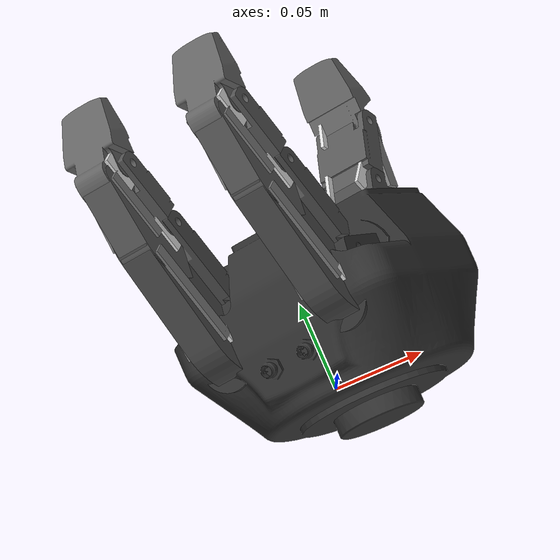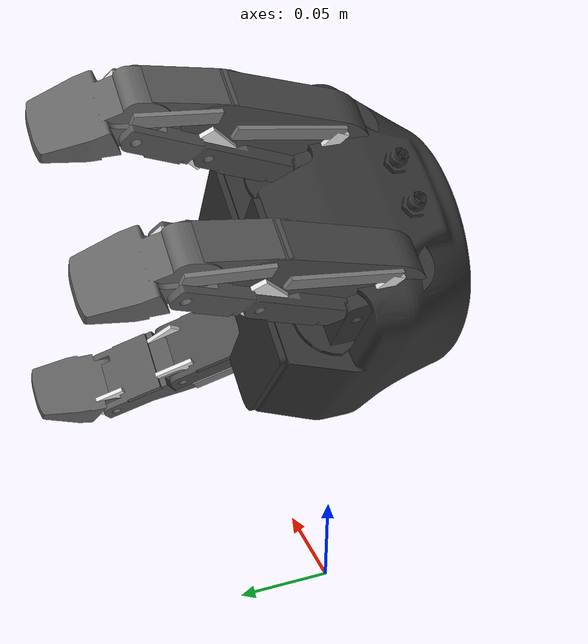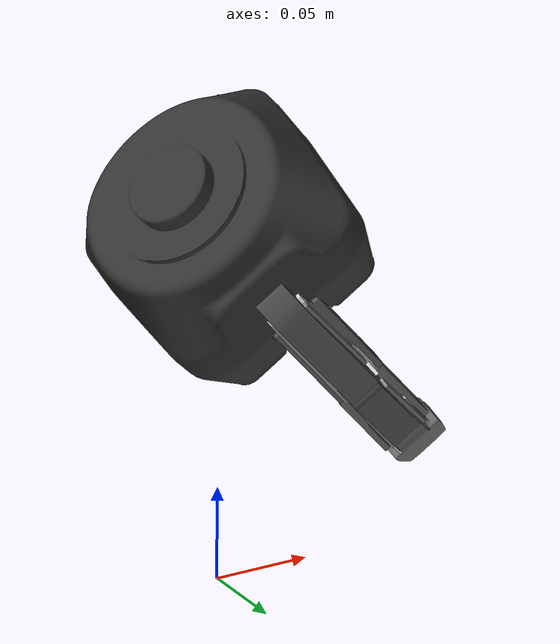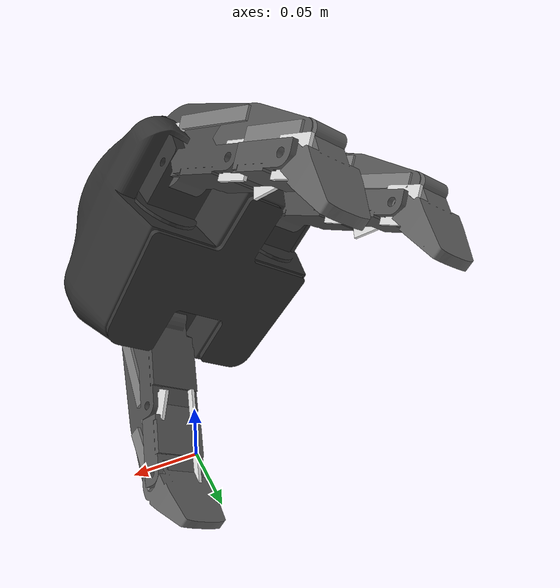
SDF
<sdf version='1.7'>
<model name='robotiq'>
  <joint name='l_robotiq_hand_joint' type='fixed'>
    <pose relative_to='__model__'>0 0 0.1 0 1 0</pose>
    <parent>world</parent>
    <child>l_palm</child>
  </joint>
  <link name='l_palm'>
    <pose relative_to='l_robotiq_hand_joint'>0 0 0 0 -0 0</pose>
    <inertial>
      <pose>0 0 0 0 -0 0</pose>
      <mass>1.3</mass>
      <inertia>
        <ixx>0.0035</ixx>
        <ixy>0</ixy>
        <ixz>0</ixz>
        <iyy>0.0035</iyy>
        <iyz>0</iyz>
        <izz>0.0035</izz>
      </inertia>
    </inertial>
    <collision name='l_palm_collision'>
      <pose>0 0 0 0 -0 0</pose>
      <geometry>
        <box>
          <size>0.1 0.1 0.1</size>
        </box>
      </geometry>
      <surface>
        <contact>
          <ode/>
        </contact>
        <friction>
          <ode>
            <mu>1.1</mu>
            <mu2>1.1</mu2>
          </ode>
          <torsional>
            <ode/>
          </torsional>
        </friction>
        <bounce/>
      </surface>
      <max_contacts>10</max_contacts>
    </collision>
    <visual name='l_palm_visual'>
      <pose>0 0 0 0 -0 0</pose>
      <geometry>
        <mesh>
          <scale>1 1 1</scale>
          <uri>/home/peter/catkin_ws/src/robotiq/robotiq_3f_gripper_visualization/meshes/robotiq-3f-gripper_articulated/visual/palm.dae</uri>
        </mesh>
      </geometry>
      <material>
        <diffuse>0.2 0.2 0.2 1</diffuse>
        <ambient>0.2 0.2 0.2 1</ambient>
        <specular>1 1 1 1</specular>
      </material>
    </visual>
    <gravity>1</gravity>
    <velocity_decay/>
    <self_collide>0</self_collide>
    <enable_wind>0</enable_wind>
    <kinematic>0</kinematic>
  </link>
  <joint name='l_palm_finger_1_joint' type='revolute'>
    <pose relative_to='l_palm'>-0.0455 0.0214 0.036 3.14159 -7e-06 1.57159</pose>
    <parent>l_palm</parent>
    <child>l_finger_1_link_0</child>
    <axis>
      <xyz>0 1 0</xyz>
      <limit>
        <lower>-0.2967</lower>
        <upper>0.2967</upper>
        <effort>60</effort>
        <velocity>-1</velocity>
      </limit>
      <dynamics>
        <damping>1</damping>
        <friction>0</friction>
        <spring_reference>0</spring_reference>
      </dynamics>
    </axis>
    <physics>
      <ode>
        <implicit_spring_damper>1</implicit_spring_damper>
        <cfm_damping>1</cfm_damping>
        <limit>
          <cfm>0</cfm>
          <erp>0.2</erp>
        </limit>
      </ode>
    </physics>
  </joint>
  <link name='l_finger_1_link_0'>
    <pose relative_to='l_palm_finger_1_joint'>0 0 0 0 -0 0</pose>
    <inertial>
      <pose>-0.01 0 0 0 -0 0</pose>
      <mass>0.1</mass>
      <inertia>
        <ixx>1.8e-05</ixx>
        <ixy>0</ixy>
        <ixz>0</ixz>
        <iyy>2.5e-05</iyy>
        <iyz>0</iyz>
        <izz>2.5e-05</izz>
      </inertia>
    </inertial>
    <collision name='l_finger_1_link_0_collision'>
      <pose>0 0 0 0 -0 0</pose>
      <geometry>
        <mesh>
          <scale>1 1 1</scale>
          <uri>/home/peter/catkin_ws/src/robotiq/robotiq_3f_gripper_visualization/meshes/robotiq-3f-gripper_articulated/collision/link_0.STL</uri>
        </mesh>
      </geometry>
      <surface>
        <contact>
          <ode/>
        </contact>
        <friction>
          <ode>
            <mu>1.1</mu>
            <mu2>1.1</mu2>
          </ode>
          <torsional>
            <ode/>
          </torsional>
        </friction>
        <bounce/>
      </surface>
      <max_contacts>10</max_contacts>
    </collision>
    <visual name='l_finger_1_link_0_visual'>
      <pose>0 0 0 0 -0 0</pose>
      <geometry>
        <mesh>
          <scale>1 1 1</scale>
          <uri>/home/peter/catkin_ws/src/robotiq/robotiq_3f_gripper_visualization/meshes/robotiq-3f-gripper_articulated/visual/link_0.dae</uri>
        </mesh>
      </geometry>
      <material>
        <diffuse>0.2 0.2 0.2 1</diffuse>
        <ambient>0.2 0.2 0.2 1</ambient>
        <specular>1 1 1 1</specular>
      </material>
    </visual>
    <gravity>1</gravity>
    <velocity_decay/>
    <self_collide>0</self_collide>
    <enable_wind>0</enable_wind>
    <kinematic>0</kinematic>
  </link>
  <joint name='l_finger_1_joint_1' type='revolute'>
    <pose relative_to='l_finger_1_link_0'>0 0 0 0 0 -2.0906</pose>
    <parent>l_finger_1_link_0</parent>
    <child>l_finger_1_link_1</child>
    <axis>
      <xyz>0 0 1</xyz>
      <limit>
        <lower>0</lower>
        <upper>1.2217</upper>
        <effort>60</effort>
        <velocity>-1</velocity>
      </limit>
      <dynamics>
        <damping>1</damping>
        <friction>0</friction>
        <spring_reference>0</spring_reference>
      </dynamics>
    </axis>
    <physics>
      <ode>
        <implicit_spring_damper>1</implicit_spring_damper>
        <cfm_damping>1</cfm_damping>
        <limit>
          <cfm>0</cfm>
          <erp>0.2</erp>
        </limit>
      </ode>
    </physics>
  </joint>
  <link name='l_finger_1_link_1'>
    <pose relative_to='l_finger_1_joint_1'>0 0 0 0 -0 0</pose>
    <inertial>
      <pose>0.00053 0.03218 0 0 -0 1.5708</pose>
      <mass>0.047</mass>
      <inertia>
        <ixx>4.99332e-06</ixx>
        <ixy>9.1312e-07</ixy>
        <ixz>-1.2e-09</ixz>
        <iyy>6.43453e-05</iyy>
        <iyz>-7e-11</iyz>
        <izz>6.06192e-05</izz>
      </inertia>
    </inertial>
    <collision name='l_finger_1_link_1_collision'>
      <pose>0 0.05717 0 0 -0 1.5708</pose>
      <geometry>
        <mesh>
          <scale>1 1 1</scale>
          <uri>/home/peter/catkin_ws/src/robotiq/robotiq_3f_gripper_visualization/meshes/robotiq-3f-gripper_articulated/collision/link_1.STL</uri>
        </mesh>
      </geometry>
      <surface>
        <contact>
          <ode/>
        </contact>
        <friction>
          <ode>
            <mu>1.1</mu>
            <mu2>1.1</mu2>
          </ode>
          <torsional>
            <ode/>
          </torsional>
        </friction>
        <bounce/>
      </surface>
      <max_contacts>10</max_contacts>
    </collision>
    <visual name='l_finger_1_link_1_visual'>
      <pose>0 0.05717 0 0 -0 1.5708</pose>
      <geometry>
        <mesh>
          <scale>1 1 1</scale>
          <uri>/home/peter/catkin_ws/src/robotiq/robotiq_3f_gripper_visualization/meshes/robotiq-3f-gripper_articulated/visual/link_1.dae</uri>
        </mesh>
      </geometry>
      <material>
        <diffuse>0.3 0.3 0.3 1</diffuse>
        <ambient>0.2 0.2 0.2 1</ambient>
        <specular>1 1 1 1</specular>
      </material>
    </visual>
    <gravity>1</gravity>
    <velocity_decay/>
    <self_collide>0</self_collide>
    <enable_wind>0</enable_wind>
    <kinematic>0</kinematic>
  </link>
  <joint name='l_finger_1_joint_2' type='revolute'>
    <pose relative_to='l_finger_1_link_1'>0 0.05715 0 0 -0 0</pose>
    <parent>l_finger_1_link_1</parent>
    <child>l_finger_1_link_2</child>
    <axis>
      <xyz>0 0 1</xyz>
      <limit>
        <lower>0</lower>
        <upper>1.5708</upper>
        <effort>60</effort>
        <velocity>-1</velocity>
      </limit>
      <dynamics>
        <damping>1</damping>
        <friction>0</friction>
        <spring_reference>0</spring_reference>
      </dynamics>
    </axis>
    <physics>
      <ode>
        <implicit_spring_damper>1</implicit_spring_damper>
        <cfm_damping>1</cfm_damping>
        <limit>
          <cfm>0</cfm>
          <erp>0.2</erp>
        </limit>
      </ode>
    </physics>
  </joint>
  <link name='l_finger_1_link_2'>
    <pose relative_to='l_finger_1_joint_2'>0 0 0 0 -0 0</pose>
    <inertial>
      <pose>0.00048 0.02167 0.00018 0 -0 1.5708</pose>
      <mass>0.03284</mass>
      <inertia>
        <ixx>3.48008e-06</ixx>
        <ixy>3.194e-07</ixy>
        <ixz>1.3041e-07</ixz>
        <iyy>2.24812e-05</iyy>
        <iyz>2.91e-09</iyz>
        <izz>1.98635e-05</izz>
      </inertia>
    </inertial>
    <collision name='l_finger_1_link_2_collision'>
      <pose>0 0.0381 0.0075 0 -0 1.5708</pose>
      <geometry>
        <mesh>
          <scale>1 1 1</scale>
          <uri>/home/peter/catkin_ws/src/robotiq/robotiq_3f_gripper_visualization/meshes/robotiq-3f-gripper_articulated/collision/link_2.STL</uri>
        </mesh>
      </geometry>
      <surface>
        <contact>
          <ode/>
        </contact>
        <friction>
          <ode>
            <mu>1.1</mu>
            <mu2>1.1</mu2>
          </ode>
          <torsional>
            <ode/>
          </torsional>
        </friction>
        <bounce/>
      </surface>
      <max_contacts>10</max_contacts>
    </collision>
    <visual name='l_finger_1_link_2_visual'>
      <pose>0 0.0381 0.0075 0 -0 1.5708</pose>
      <geometry>
        <mesh>
          <scale>1 1 1</scale>
          <uri>/home/peter/catkin_ws/src/robotiq/robotiq_3f_gripper_visualization/meshes/robotiq-3f-gripper_articulated/visual/link_2.dae</uri>
        </mesh>
      </geometry>
      <material>
        <diffuse>0.35 0.35 0.35 1</diffuse>
        <ambient>0.35 0.35 0.35 1</ambient>
        <specular>1 1 1 1</specular>
      </material>
    </visual>
    <gravity>1</gravity>
    <velocity_decay/>
    <self_collide>0</self_collide>
    <enable_wind>0</enable_wind>
    <kinematic>0</kinematic>
  </link>
  <joint name='l_finger_1_joint_3' type='revolute'>
    <pose relative_to='l_finger_1_link_2'>0 0.039 0 0 -0 2.0906</pose>
    <parent>l_finger_1_link_2</parent>
    <child>l_finger_1_link_3</child>
    <axis>
      <xyz>0 0 1</xyz>
      <limit>
        <lower>-0.6632</lower>
        <upper>1.0471</upper>
        <effort>60</effort>
        <velocity>-1</velocity>
      </limit>
      <dynamics>
        <damping>1</damping>
        <friction>0</friction>
        <spring_reference>0</spring_reference>
      </dynamics>
    </axis>
    <physics>
      <ode>
        <implicit_spring_damper>1</implicit_spring_damper>
        <cfm_damping>1</cfm_damping>
        <limit>
          <cfm>0</cfm>
          <erp>0.2</erp>
        </limit>
      </ode>
    </physics>
  </joint>
  <link name='l_finger_1_link_3'>
    <pose relative_to='l_finger_1_joint_3'>0 0 0 0 -0 0</pose>
    <inertial>
      <pose>0.01626 0.00049 0.0002 0 -0 0</pose>
      <mass>0.03354</mass>
      <inertia>
        <ixx>3.05151e-06</ixx>
        <ixy>8.9792e-07</ixy>
        <ixz>2.49e-09</ixz>
        <iyy>1.42798e-05</iyy>
        <iyz>-1.191e-08</iyz>
        <izz>1.26413e-05</izz>
      </inertia>
    </inertial>
    <collision name='l_finger_1_link_3_collision'>
      <pose>0 0 0 0 -0 0</pose>
      <geometry>
        <mesh>
          <scale>1 1 1</scale>
          <uri>/home/peter/catkin_ws/src/robotiq/robotiq_3f_gripper_visualization/meshes/robotiq-3f-gripper_articulated/collision/link_3.STL</uri>
        </mesh>
      </geometry>
      <surface>
        <contact>
          <ode/>
        </contact>
        <friction>
          <ode>
            <mu>1.1</mu>
            <mu2>1.1</mu2>
          </ode>
          <torsional>
            <ode/>
          </torsional>
        </friction>
        <bounce/>
      </surface>
      <max_contacts>10</max_contacts>
    </collision>
    <visual name='l_finger_1_link_3_visual'>
      <pose>0 0 0 0 -0 0</pose>
      <geometry>
        <mesh>
          <scale>1 1 1</scale>
          <uri>/home/peter/catkin_ws/src/robotiq/robotiq_3f_gripper_visualization/meshes/robotiq-3f-gripper_articulated/visual/link_3.dae</uri>
        </mesh>
      </geometry>
      <material>
        <diffuse>0.4 0.4 0.4 1</diffuse>
        <ambient>0.3 0.3 0.3 1</ambient>
        <specular>1 1 1 1</specular>
      </material>
    </visual>
    <gravity>1</gravity>
    <velocity_decay/>
    <self_collide>0</self_collide>
    <enable_wind>0</enable_wind>
    <kinematic>0</kinematic>
  </link>
  <joint name='l_finger_1_joint_paradistal_hinge' type='revolute'>
    <pose relative_to='l_finger_1_link_2'>0 0.039 -0.01 0 -0 0</pose>
    <parent>l_finger_1_link_2</parent>
    <child>l_finger_1_link_paradistal_hinge</child>
    <axis>
      <xyz>0 0 1</xyz>
      <limit>
        <lower>-3.1416</lower>
        <upper>3.1416</upper>
        <effort>100</effort>
        <velocity>100</velocity>
      </limit>
      <dynamics>
        <spring_reference>0</spring_reference>
      </dynamics>
    </axis>
    <physics>
      <ode>
        <implicit_spring_damper>1</implicit_spring_damper>
        <cfm_damping>1</cfm_damping>
        <limit>
          <cfm>0</cfm>
          <erp>0.2</erp>
        </limit>
      </ode>
    </physics>
  </joint>
  <link name='l_finger_1_link_paradistal_hinge'>
    <pose relative_to='l_finger_1_joint_paradistal_hinge'>0 0 0 0 -0 0</pose>
    <inertial>
      <pose>0.00548 0 0 0 -0 0</pose>
      <mass>0.00158</mass>
      <inertia>
        <ixx>1.907e-08</ixx>
        <ixy>0</ixy>
        <ixz>0</ixz>
        <iyy>1.097e-07</iyy>
        <iyz>0</iyz>
        <izz>1.261e-07</izz>
      </inertia>
    </inertial>
    <collision name='l_finger_1_link_paradistal_hinge_collision'>
      <pose>0 0 0 0 -0 0</pose>
      <geometry>
        <box>
          <size>0.02 0.02 0.002</size>
        </box>
      </geometry>
      <surface>
        <contact>
          <ode/>
        </contact>
        <friction>
          <ode>
            <mu>1.1</mu>
            <mu2>1.1</mu2>
          </ode>
          <torsional>
            <ode/>
          </torsional>
        </friction>
        <bounce/>
      </surface>
      <max_contacts>10</max_contacts>
    </collision>
    <visual name='l_finger_1_link_paradistal_hinge_visual'>
      <pose>0 0 0 0 -0 0</pose>
      <geometry>
        <box>
          <size>0.02 0.02 0.002</size>
        </box>
      </geometry>
      <material>
        <diffuse>0.9 0.9 0.9 1</diffuse>
        <ambient>0.5 0.5 0.5 1</ambient>
        <specular>1 1 1 1</specular>
      </material>
    </visual>
    <gravity>1</gravity>
    <velocity_decay/>
    <self_collide>0</self_collide>
    <enable_wind>0</enable_wind>
    <kinematic>0</kinematic>
  </link>
  <joint name='l_finger_1_joint_median_actuating_hinge' type='revolute'>
    <pose relative_to='l_finger_1_link_1'>0 0.05715 0.01 0 0 -0.37</pose>
    <parent>l_finger_1_link_1</parent>
    <child>l_finger_1_link_median_actuating_hinge</child>
    <axis>
      <xyz>0 0 1</xyz>
      <limit>
        <lower>-3.1416</lower>
        <upper>3.1416</upper>
        <effort>100</effort>
        <velocity>100</velocity>
      </limit>
      <dynamics>
        <spring_reference>0</spring_reference>
      </dynamics>
    </axis>
    <physics>
      <ode>
        <implicit_spring_damper>1</implicit_spring_damper>
        <cfm_damping>1</cfm_damping>
        <limit>
          <cfm>0</cfm>
          <erp>0.2</erp>
        </limit>
      </ode>
    </physics>
  </joint>
  <link name='l_finger_1_link_median_actuating_hinge'>
    <pose relative_to='l_finger_1_joint_median_actuating_hinge'>0 0 0 0 -0 0</pose>
    <inertial>
      <pose>0.0092 0.00514 0 0 -0 0</pose>
      <mass>0.00359</mass>
      <inertia>
        <ixx>2.4735e-07</ixx>
        <ixy>2.3619e-07</ixy>
        <ixz>0</ixz>
        <iyy>4.7681e-07</iyy>
        <iyz>0</iyz>
        <izz>7.1813e-07</izz>
      </inertia>
    </inertial>
    <collision name='l_finger_1_link_median_actuating_hinge_collision'>
      <pose>0 0 0 0 -0 0</pose>
      <geometry>
        <box>
          <size>0.02 0.02 0.002</size>
        </box>
      </geometry>
      <surface>
        <contact>
          <ode/>
        </contact>
        <friction>
          <ode>
            <mu>1.1</mu>
            <mu2>1.1</mu2>
          </ode>
          <torsional>
            <ode/>
          </torsional>
        </friction>
        <bounce/>
      </surface>
      <max_contacts>10</max_contacts>
    </collision>
    <visual name='l_finger_1_link_median_actuating_hinge_visual'>
      <pose>0 0 0 0 -0 0</pose>
      <geometry>
        <box>
          <size>0.02 0.02 0.002</size>
        </box>
      </geometry>
      <material>
        <diffuse>0.9 0.9 0.9 1</diffuse>
        <ambient>0.5 0.5 0.5 1</ambient>
        <specular>1 1 1 1</specular>
      </material>
    </visual>
    <gravity>1</gravity>
    <velocity_decay/>
    <self_collide>0</self_collide>
    <enable_wind>0</enable_wind>
    <kinematic>0</kinematic>
  </link>
  <joint name='l_finger_1_joint_median_actuating_hinge_median_bar' type='revolute'>
    <pose relative_to='l_finger_1_link_median_actuating_hinge'>0.01625 0.01516 0 0 -0 2.3215</pose>
    <parent>l_finger_1_link_median_actuating_hinge</parent>
    <child>l_finger_1_link_median_bar</child>
    <axis>
      <xyz>0 0 1</xyz>
      <limit>
        <lower>-3.1416</lower>
        <upper>3.1416</upper>
        <effort>100</effort>
        <velocity>100</velocity>
      </limit>
      <dynamics>
        <spring_reference>0</spring_reference>
      </dynamics>
    </axis>
    <physics>
      <ode>
        <implicit_spring_damper>1</implicit_spring_damper>
        <cfm_damping>1</cfm_damping>
        <limit>
          <cfm>0</cfm>
          <erp>0.2</erp>
        </limit>
      </ode>
    </physics>
  </joint>
  <link name='l_finger_1_link_median_bar'>
    <pose relative_to='l_finger_1_joint_median_actuating_hinge_median_bar'>0 0 0 0 -0 0</pose>
    <inertial>
      <pose>0.01905 -0.00107 0 0 -0 0</pose>
      <mass>0.00538</mass>
      <inertia>
        <ixx>6.639e-08</ixx>
        <ixy>-1.0996e-07</ixy>
        <ixz>9.4e-10</ixz>
        <iyy>3.05318e-06</iyy>
        <iyz>0</iyz>
        <izz>3.04657e-06</izz>
      </inertia>
    </inertial>
    <collision name='l_finger_1_link_median_bar_collision'>
      <pose>0.01905 0 0 0 -0 0</pose>
      <geometry>
        <box>
          <size>0.0381 0.0075 0.002</size>
        </box>
      </geometry>
      <surface>
        <contact>
          <ode/>
        </contact>
        <friction>
          <ode>
            <mu>1.1</mu>
            <mu2>1.1</mu2>
          </ode>
          <torsional>
            <ode/>
          </torsional>
        </friction>
        <bounce/>
      </surface>
      <max_contacts>10</max_contacts>
    </collision>
    <visual name='l_finger_1_link_median_bar_visual'>
      <pose>0.01905 0 0 0 -0 0</pose>
      <geometry>
        <box>
          <size>0.0381 0.0075 0.002</size>
        </box>
      </geometry>
      <material>
        <diffuse>0.5 0.5 0.5 1</diffuse>
        <ambient>0.4 0.4 0.4 1</ambient>
        <specular>1 1 1 1</specular>
      </material>
    </visual>
    <gravity>1</gravity>
    <velocity_decay/>
    <self_collide>0</self_collide>
    <enable_wind>0</enable_wind>
    <kinematic>0</kinematic>
  </link>
  <joint name='l_finger_1_joint_paramedian_hinge' type='revolute'>
    <pose relative_to='l_finger_1_link_1'>0 0.05715 -0.01 0 -0 0</pose>
    <parent>l_finger_1_link_1</parent>
    <child>l_finger_1_link_paramedian_hinge</child>
    <axis>
      <xyz>0 0 1</xyz>
      <limit>
        <lower>-3.1416</lower>
        <upper>3.1416</upper>
        <effort>100</effort>
        <velocity>100</velocity>
      </limit>
      <dynamics>
        <spring_reference>0</spring_reference>
      </dynamics>
    </axis>
    <physics>
      <ode>
        <implicit_spring_damper>1</implicit_spring_damper>
        <cfm_damping>1</cfm_damping>
        <limit>
          <cfm>0</cfm>
          <erp>0.2</erp>
        </limit>
      </ode>
    </physics>
  </joint>
  <link name='l_finger_1_link_paramedian_hinge'>
    <pose relative_to='l_finger_1_joint_paramedian_hinge'>0 0 0 0 -0 0</pose>
    <inertial>
      <pose>-0.01025 0.00046 0 0 -0 0</pose>
      <mass>0.00276</mass>
      <inertia>
        <ixx>4.213e-08</ixx>
        <ixy>-1.491e-08</ixy>
        <ixz>0</ixz>
        <iyy>5.0258e-07</iyy>
        <iyz>0</iyz>
        <izz>5.4007e-07</izz>
      </inertia>
    </inertial>
    <collision name='l_finger_1_link_paramedian_hinge_collision'>
      <pose>0 0 0 0 -0 0</pose>
      <geometry>
        <box>
          <size>0.02 0.02 0.002</size>
        </box>
      </geometry>
      <surface>
        <contact>
          <ode/>
        </contact>
        <friction>
          <ode>
            <mu>1.1</mu>
            <mu2>1.1</mu2>
          </ode>
          <torsional>
            <ode/>
          </torsional>
        </friction>
        <bounce/>
      </surface>
      <max_contacts>10</max_contacts>
    </collision>
    <visual name='l_finger_1_link_paramedian_hinge_visual'>
      <pose>0 0 0 0 -0 0</pose>
      <geometry>
        <box>
          <size>0.02 0.02 0.002</size>
        </box>
      </geometry>
      <material>
        <diffuse>0.9 0.9 0.9 1</diffuse>
        <ambient>0.5 0.5 0.5 1</ambient>
        <specular>1 1 1 1</specular>
      </material>
    </visual>
    <gravity>1</gravity>
    <velocity_decay/>
    <self_collide>0</self_collide>
    <enable_wind>0</enable_wind>
    <kinematic>0</kinematic>
  </link>
  <joint name='l_finger_1_joint_paramedian_hinge_median_bar_underactuated' type='revolute'>
    <pose relative_to='l_finger_1_link_paramedian_hinge'>0.01227 0.00329 0 0 -0 1.5708</pose>
    <parent>l_finger_1_link_paramedian_hinge</parent>
    <child>l_finger_1_link_median_bar_underactuated</child>
    <axis>
      <xyz>0 0 1</xyz>
      <limit>
        <lower>-3.1416</lower>
        <upper>3.1416</upper>
        <effort>100</effort>
        <velocity>100</velocity>
      </limit>
      <dynamics>
        <spring_reference>0</spring_reference>
      </dynamics>
    </axis>
    <physics>
      <ode>
        <implicit_spring_damper>1</implicit_spring_damper>
        <cfm_damping>1</cfm_damping>
        <limit>
          <cfm>0</cfm>
          <erp>0.2</erp>
        </limit>
      </ode>
    </physics>
  </joint>
  <link name='l_finger_1_link_median_bar_underactuated'>
    <pose relative_to='l_finger_1_joint_paramedian_hinge_median_bar_underactuated'>0 0 0 0 -0 0</pose>
    <inertial>
      <pose>0.01905 -0.00107 0 0 -0 0</pose>
      <mass>0.00538</mass>
      <inertia>
        <ixx>6.639e-08</ixx>
        <ixy>-1.0996e-07</ixy>
        <ixz>-9.4e-10</ixz>
        <iyy>3.05318e-06</iyy>
        <iyz>0</iyz>
        <izz>3.04657e-06</izz>
      </inertia>
    </inertial>
    <collision name='l_finger_1_link_median_bar_underactuated_collision'>
      <pose>0.01905 0 0 0 -0 0</pose>
      <geometry>
        <box>
          <size>0.0381 0.0075 0.002</size>
        </box>
      </geometry>
      <surface>
        <contact>
          <ode/>
        </contact>
        <friction>
          <ode>
            <mu>1.1</mu>
            <mu2>1.1</mu2>
          </ode>
          <torsional>
            <ode/>
          </torsional>
        </friction>
        <bounce/>
      </surface>
      <max_contacts>10</max_contacts>
    </collision>
    <visual name='l_finger_1_link_median_bar_underactuated_visual'>
      <pose>0.01905 0 0 0 -0 0</pose>
      <geometry>
        <box>
          <size>0.0381 0.0075 0.002</size>
        </box>
      </geometry>
      <material>
        <diffuse>0.5 0.5 0.5 1</diffuse>
        <ambient>0.4 0.4 0.4 1</ambient>
        <specular>1 1 1 1</specular>
      </material>
    </visual>
    <gravity>1</gravity>
    <velocity_decay/>
    <self_collide>0</self_collide>
    <enable_wind>0</enable_wind>
    <kinematic>0</kinematic>
  </link>
  <joint name='l_finger_1_joint_paraproximal_actuating_hinge' type='revolute'>
    <pose relative_to='l_finger_1_link_0'>0 0 -0.01 0 0 -2.0906</pose>
    <parent>l_finger_1_link_0</parent>
    <child>l_finger_1_link_paraproximal_actuating_hinge</child>
    <axis>
      <xyz>0 0 1</xyz>
      <limit>
        <lower>-3.1416</lower>
        <upper>3.1416</upper>
        <effort>100</effort>
        <velocity>100</velocity>
      </limit>
      <dynamics>
        <spring_reference>0</spring_reference>
        <spring_stiffness>1</spring_stiffness>
      </dynamics>
    </axis>
    <physics>
      <ode>
        <implicit_spring_damper>1</implicit_spring_damper>
        <cfm_damping>1</cfm_damping>
        <limit>
          <cfm>0</cfm>
          <erp>0.2</erp>
        </limit>
      </ode>
    </physics>
  </joint>
  <link name='l_finger_1_link_paraproximal_actuating_hinge'>
    <pose relative_to='l_finger_1_joint_paraproximal_actuating_hinge'>0 0 0 0 -0 0</pose>
    <inertial>
      <pose>0.0064 0 0 0 -0 0</pose>
      <mass>0.00362</mass>
      <inertia>
        <ixx>1.2043e-07</ixx>
        <ixy>0</ixy>
        <ixz>0</ixz>
        <iyy>5.3588e-07</iyy>
        <iyz>0</iyz>
        <izz>6.5322e-07</izz>
      </inertia>
    </inertial>
    <collision name='l_finger_1_link_paraproximal_actuating_hinge_collision'>
      <pose>0.01143 0 0 0 -0 0</pose>
      <geometry>
        <box>
          <size>0.02286 0.0075 0.002</size>
        </box>
      </geometry>
      <surface>
        <contact>
          <ode/>
        </contact>
        <friction>
          <ode>
            <mu>1.1</mu>
            <mu2>1.1</mu2>
          </ode>
          <torsional>
            <ode/>
          </torsional>
        </friction>
        <bounce/>
      </surface>
      <max_contacts>10</max_contacts>
    </collision>
    <visual name='l_finger_1_link_paraproximal_actuating_hinge_visual'>
      <pose>0.01143 0 0 0 -0 0</pose>
      <geometry>
        <box>
          <size>0.02286 0.0075 0.002</size>
        </box>
      </geometry>
      <material>
        <diffuse>0.9 0.9 0.9 1</diffuse>
        <ambient>0.5 0.5 0.5 1</ambient>
        <specular>1 1 1 1</specular>
      </material>
    </visual>
    <gravity>1</gravity>
    <velocity_decay/>
    <self_collide>0</self_collide>
    <enable_wind>0</enable_wind>
    <kinematic>0</kinematic>
  </link>
  <joint name='l_finger_1_joint_paraproximal_bar' type='revolute'>
    <pose relative_to='l_finger_1_link_paraproximal_actuating_hinge'>0.02286 0 0 0 -0 1.57</pose>
    <parent>l_finger_1_link_paraproximal_actuating_hinge</parent>
    <child>l_finger_1_link_paraproximal_bar</child>
    <axis>
      <xyz>0 0 1</xyz>
      <limit>
        <lower>-3.1416</lower>
        <upper>3.1416</upper>
        <effort>100</effort>
        <velocity>100</velocity>
      </limit>
      <dynamics>
        <spring_reference>0</spring_reference>
      </dynamics>
    </axis>
    <physics>
      <ode>
        <implicit_spring_damper>1</implicit_spring_damper>
        <cfm_damping>1</cfm_damping>
        <limit>
          <cfm>0</cfm>
          <erp>0.2</erp>
        </limit>
      </ode>
    </physics>
  </joint>
  <link name='l_finger_1_link_paraproximal_bar'>
    <pose relative_to='l_finger_1_joint_paraproximal_bar'>0 0 0 0 -0 0</pose>
    <inertial>
      <pose>0.02858 -0.00129 0 0 -0 0</pose>
      <mass>0.00732</mass>
      <inertia>
        <ixx>9.065e-08</ixx>
        <ixy>-2.7047e-07</ixy>
        <ixz>1.42e-09</ixz>
        <iyy>8.78034e-06</iyy>
        <iyz>0</iyz>
        <izz>8.77558e-06</izz>
      </inertia>
    </inertial>
    <collision name='l_finger_1_link_paraproximal_bar_collision'>
      <pose>0.02885 0 0 0 -0 0</pose>
      <geometry>
        <box>
          <size>0.0577 0.0075 0.002</size>
        </box>
      </geometry>
      <surface>
        <contact>
          <ode/>
        </contact>
        <friction>
          <ode>
            <mu>1.1</mu>
            <mu2>1.1</mu2>
          </ode>
          <torsional>
            <ode/>
          </torsional>
        </friction>
        <bounce/>
      </surface>
      <max_contacts>10</max_contacts>
    </collision>
    <visual name='l_finger_1_link_paraproximal_bar_visual'>
      <pose>0.02885 0 0 0 -0 0</pose>
      <geometry>
        <box>
          <size>0.0577 0.0075 0.002</size>
        </box>
      </geometry>
      <material>
        <diffuse>0.5 0.5 0.5 1</diffuse>
        <ambient>0.4 0.4 0.4 1</ambient>
        <specular>1 1 1 1</specular>
      </material>
    </visual>
    <gravity>1</gravity>
    <velocity_decay/>
    <self_collide>0</self_collide>
    <enable_wind>0</enable_wind>
    <kinematic>0</kinematic>
  </link>
  <joint name='l_finger_1_joint_proximal_actuating_hinge' type='revolute'>
    <pose relative_to='l_finger_1_link_0'>0 0 0.01 0 0 -2.0906</pose>
    <parent>l_finger_1_link_0</parent>
    <child>l_finger_1_link_proximal_actuating_hinge</child>
    <axis>
      <xyz>0 0 1</xyz>
      <limit>
        <lower>-3.1416</lower>
        <upper>3.1416</upper>
        <effort>100</effort>
        <velocity>100</velocity>
      </limit>
      <dynamics>
        <spring_reference>0</spring_reference>
      </dynamics>
    </axis>
    <physics>
      <ode>
        <implicit_spring_damper>1</implicit_spring_damper>
        <cfm_damping>1</cfm_damping>
        <limit>
          <cfm>0</cfm>
          <erp>0.2</erp>
        </limit>
      </ode>
    </physics>
  </joint>
  <link name='l_finger_1_link_proximal_actuating_hinge'>
    <pose relative_to='l_finger_1_joint_proximal_actuating_hinge'>0 0 0 0 -0 0</pose>
    <inertial>
      <pose>0.0012 -0.00162 -0.00161 0 -0 0</pose>
      <mass>0.02647</mass>
      <inertia>
        <ixx>1.56447e-06</ixx>
        <ixy>2.36226e-07</ixy>
        <ixz>-1.4862e-07</ixz>
        <iyy>2.21068e-06</iyy>
        <iyz>-1.4369e-07</iyz>
        <izz>3.23175e-06</izz>
      </inertia>
    </inertial>
    <collision name='l_finger_1_link_proximal_actuating_hinge_collision'>
      <pose>0.01429 0 0 0 -0 0</pose>
      <geometry>
        <box>
          <size>0.02858 0.0075 0.002</size>
        </box>
      </geometry>
      <surface>
        <contact>
          <ode/>
        </contact>
        <friction>
          <ode>
            <mu>1.1</mu>
            <mu2>1.1</mu2>
          </ode>
          <torsional>
            <ode/>
          </torsional>
        </friction>
        <bounce/>
      </surface>
      <max_contacts>10</max_contacts>
    </collision>
    <visual name='l_finger_1_link_proximal_actuating_hinge_visual'>
      <pose>0.01429 0 0 0 -0 0</pose>
      <geometry>
        <box>
          <size>0.02858 0.0075 0.002</size>
        </box>
      </geometry>
      <material>
        <diffuse>0.9 0.9 0.9 1</diffuse>
        <ambient>0.5 0.5 0.5 1</ambient>
        <specular>1 1 1 1</specular>
      </material>
    </visual>
    <gravity>1</gravity>
    <velocity_decay/>
    <self_collide>0</self_collide>
    <enable_wind>0</enable_wind>
    <kinematic>0</kinematic>
  </link>
  <joint name='l_finger_1_joint_proximal_actuating_bar' type='revolute'>
    <pose relative_to='l_finger_1_link_proximal_actuating_hinge'>0.02858 0 0 0 -0 1.8616</pose>
    <parent>l_finger_1_link_proximal_actuating_hinge</parent>
    <child>l_finger_1_link_proximal_actuating_bar</child>
    <axis>
      <xyz>0 0 1</xyz>
      <limit>
        <lower>-3.1416</lower>
        <upper>3.1416</upper>
        <effort>100</effort>
        <velocity>100</velocity>
      </limit>
      <dynamics>
        <spring_reference>0</spring_reference>
      </dynamics>
    </axis>
    <physics>
      <ode>
        <implicit_spring_damper>1</implicit_spring_damper>
        <cfm_damping>1</cfm_damping>
        <limit>
          <cfm>0</cfm>
          <erp>0.2</erp>
        </limit>
      </ode>
    </physics>
  </joint>
  <link name='l_finger_1_link_proximal_actuating_bar'>
    <pose relative_to='l_finger_1_joint_proximal_actuating_bar'>0 0 0 0 -0 0</pose>
    <inertial>
      <pose>0.02699 -0.00122 0 0 -0 0</pose>
      <mass>0.00659</mass>
      <inertia>
        <ixx>8.348e-08</ixx>
        <ixy>-2.179e-07</ixy>
        <ixz>1.34e-09</ixz>
        <iyy>7.19076e-06</iyy>
        <iyz>0</iyz>
        <izz>7.18272e-06</izz>
      </inertia>
    </inertial>
    <collision name='l_finger_1_link_proximal_actuating_bar_collision'>
      <pose>0.026789 0 0 0 -0 0</pose>
      <geometry>
        <box>
          <size>0.05398 0.0075 0.002</size>
        </box>
      </geometry>
      <surface>
        <contact>
          <ode/>
        </contact>
        <friction>
          <ode>
            <mu>1.1</mu>
            <mu2>1.1</mu2>
          </ode>
          <torsional>
            <ode/>
          </torsional>
        </friction>
        <bounce/>
      </surface>
      <max_contacts>10</max_contacts>
    </collision>
    <visual name='l_finger_1_link_proximal_actuating_bar_visual'>
      <pose>0.026789 0 0 0 -0 0</pose>
      <geometry>
        <box>
          <size>0.05398 0.0075 0.002</size>
        </box>
      </geometry>
      <material>
        <diffuse>0.5 0.5 0.5 1</diffuse>
        <ambient>0.4 0.4 0.4 1</ambient>
        <specular>1 1 1 1</specular>
      </material>
    </visual>
    <gravity>1</gravity>
    <velocity_decay/>
    <self_collide>0</self_collide>
    <enable_wind>0</enable_wind>
    <kinematic>0</kinematic>
  </link>
  <joint name='l_palm_finger_2_joint' type='revolute'>
    <pose relative_to='l_palm'>-0.0455 0.0214 -0.036 3.14159 -7e-06 1.57159</pose>
    <parent>l_palm</parent>
    <child>l_finger_2_link_0</child>
    <axis>
      <xyz>0 1 0</xyz>
      <limit>
        <lower>-0.2967</lower>
        <upper>0.2967</upper>
        <effort>60</effort>
        <velocity>-1</velocity>
      </limit>
      <dynamics>
        <damping>1</damping>
        <friction>0</friction>
        <spring_reference>0</spring_reference>
      </dynamics>
    </axis>
    <physics>
      <ode>
        <implicit_spring_damper>1</implicit_spring_damper>
        <cfm_damping>1</cfm_damping>
        <limit>
          <cfm>0</cfm>
          <erp>0.2</erp>
        </limit>
      </ode>
    </physics>
  </joint>
  <link name='l_finger_2_link_0'>
    <pose relative_to='l_palm_finger_2_joint'>0 0 0 0 -0 0</pose>
    <inertial>
      <pose>-0.01 0 0 0 -0 0</pose>
      <mass>0.1</mass>
      <inertia>
        <ixx>1.8e-05</ixx>
        <ixy>0</ixy>
        <ixz>0</ixz>
        <iyy>2.5e-05</iyy>
        <iyz>0</iyz>
        <izz>2.5e-05</izz>
      </inertia>
    </inertial>
    <collision name='l_finger_2_link_0_collision'>
      <pose>0 0 0 0 -0 0</pose>
      <geometry>
        <mesh>
          <scale>1 1 1</scale>
          <uri>/home/peter/catkin_ws/src/robotiq/robotiq_3f_gripper_visualization/meshes/robotiq-3f-gripper_articulated/collision/link_0.STL</uri>
        </mesh>
      </geometry>
      <surface>
        <contact>
          <ode/>
        </contact>
        <friction>
          <ode>
            <mu>1.1</mu>
            <mu2>1.1</mu2>
          </ode>
          <torsional>
            <ode/>
          </torsional>
        </friction>
        <bounce/>
      </surface>
      <max_contacts>10</max_contacts>
    </collision>
    <visual name='l_finger_2_link_0_visual'>
      <pose>0 0 0 0 -0 0</pose>
      <geometry>
        <mesh>
          <scale>1 1 1</scale>
          <uri>/home/peter/catkin_ws/src/robotiq/robotiq_3f_gripper_visualization/meshes/robotiq-3f-gripper_articulated/visual/link_0.dae</uri>
        </mesh>
      </geometry>
      <material>
        <diffuse>0.2 0.2 0.2 1</diffuse>
        <ambient>0.2 0.2 0.2 1</ambient>
        <specular>1 1 1 1</specular>
      </material>
    </visual>
    <gravity>1</gravity>
    <velocity_decay/>
    <self_collide>0</self_collide>
    <enable_wind>0</enable_wind>
    <kinematic>0</kinematic>
  </link>
  <joint name='l_finger_2_joint_1' type='revolute'>
    <pose relative_to='l_finger_2_link_0'>0 0 0 0 0 -2.0906</pose>
    <parent>l_finger_2_link_0</parent>
    <child>l_finger_2_link_1</child>
    <axis>
      <xyz>0 0 1</xyz>
      <limit>
        <lower>0</lower>
        <upper>1.2217</upper>
        <effort>60</effort>
        <velocity>-1</velocity>
      </limit>
      <dynamics>
        <damping>1</damping>
        <friction>0</friction>
        <spring_reference>0</spring_reference>
      </dynamics>
    </axis>
    <physics>
      <ode>
        <implicit_spring_damper>1</implicit_spring_damper>
        <cfm_damping>1</cfm_damping>
        <limit>
          <cfm>0</cfm>
          <erp>0.2</erp>
        </limit>
      </ode>
    </physics>
  </joint>
  <link name='l_finger_2_link_1'>
    <pose relative_to='l_finger_2_joint_1'>0 0 0 0 -0 0</pose>
    <inertial>
      <pose>0.00053 0.03218 0 0 -0 1.5708</pose>
      <mass>0.047</mass>
      <inertia>
        <ixx>4.99332e-06</ixx>
        <ixy>9.1312e-07</ixy>
        <ixz>-1.2e-09</ixz>
        <iyy>6.43453e-05</iyy>
        <iyz>-7e-11</iyz>
        <izz>6.06192e-05</izz>
      </inertia>
    </inertial>
    <collision name='l_finger_2_link_1_collision'>
      <pose>0 0.05717 0 0 -0 1.5708</pose>
      <geometry>
        <mesh>
          <scale>1 1 1</scale>
          <uri>/home/peter/catkin_ws/src/robotiq/robotiq_3f_gripper_visualization/meshes/robotiq-3f-gripper_articulated/collision/link_1.STL</uri>
        </mesh>
      </geometry>
      <surface>
        <contact>
          <ode/>
        </contact>
        <friction>
          <ode>
            <mu>1.1</mu>
            <mu2>1.1</mu2>
          </ode>
          <torsional>
            <ode/>
          </torsional>
        </friction>
        <bounce/>
      </surface>
      <max_contacts>10</max_contacts>
    </collision>
    <visual name='l_finger_2_link_1_visual'>
      <pose>0 0.05717 0 0 -0 1.5708</pose>
      <geometry>
        <mesh>
          <scale>1 1 1</scale>
          <uri>/home/peter/catkin_ws/src/robotiq/robotiq_3f_gripper_visualization/meshes/robotiq-3f-gripper_articulated/visual/link_1.dae</uri>
        </mesh>
      </geometry>
      <material>
        <diffuse>0.3 0.3 0.3 1</diffuse>
        <ambient>0.2 0.2 0.2 1</ambient>
        <specular>1 1 1 1</specular>
      </material>
    </visual>
    <gravity>1</gravity>
    <velocity_decay/>
    <self_collide>0</self_collide>
    <enable_wind>0</enable_wind>
    <kinematic>0</kinematic>
  </link>
  <joint name='l_finger_2_joint_2' type='revolute'>
    <pose relative_to='l_finger_2_link_1'>0 0.05715 0 0 -0 0</pose>
    <parent>l_finger_2_link_1</parent>
    <child>l_finger_2_link_2</child>
    <axis>
      <xyz>0 0 1</xyz>
      <limit>
        <lower>0</lower>
        <upper>1.5708</upper>
        <effort>60</effort>
        <velocity>-1</velocity>
      </limit>
      <dynamics>
        <damping>1</damping>
        <friction>0</friction>
        <spring_reference>0</spring_reference>
      </dynamics>
    </axis>
    <physics>
      <ode>
        <implicit_spring_damper>1</implicit_spring_damper>
        <cfm_damping>1</cfm_damping>
        <limit>
          <cfm>0</cfm>
          <erp>0.2</erp>
        </limit>
      </ode>
    </physics>
  </joint>
  <link name='l_finger_2_link_2'>
    <pose relative_to='l_finger_2_joint_2'>0 0 0 0 -0 0</pose>
    <inertial>
      <pose>0.00048 0.02167 0.00018 0 -0 1.5708</pose>
      <mass>0.03284</mass>
      <inertia>
        <ixx>3.48008e-06</ixx>
        <ixy>3.194e-07</ixy>
        <ixz>1.3041e-07</ixz>
        <iyy>2.24812e-05</iyy>
        <iyz>2.91e-09</iyz>
        <izz>1.98635e-05</izz>
      </inertia>
    </inertial>
    <collision name='l_finger_2_link_2_collision'>
      <pose>0 0.0381 0.0075 0 -0 1.5708</pose>
      <geometry>
        <mesh>
          <scale>1 1 1</scale>
          <uri>/home/peter/catkin_ws/src/robotiq/robotiq_3f_gripper_visualization/meshes/robotiq-3f-gripper_articulated/collision/link_2.STL</uri>
        </mesh>
      </geometry>
      <surface>
        <contact>
          <ode/>
        </contact>
        <friction>
          <ode>
            <mu>1.1</mu>
            <mu2>1.1</mu2>
          </ode>
          <torsional>
            <ode/>
          </torsional>
        </friction>
        <bounce/>
      </surface>
      <max_contacts>10</max_contacts>
    </collision>
    <visual name='l_finger_2_link_2_visual'>
      <pose>0 0.0381 0.0075 0 -0 1.5708</pose>
      <geometry>
        <mesh>
          <scale>1 1 1</scale>
          <uri>/home/peter/catkin_ws/src/robotiq/robotiq_3f_gripper_visualization/meshes/robotiq-3f-gripper_articulated/visual/link_2.dae</uri>
        </mesh>
      </geometry>
      <material>
        <diffuse>0.35 0.35 0.35 1</diffuse>
        <ambient>0.35 0.35 0.35 1</ambient>
        <specular>1 1 1 1</specular>
      </material>
    </visual>
    <gravity>1</gravity>
    <velocity_decay/>
    <self_collide>0</self_collide>
    <enable_wind>0</enable_wind>
    <kinematic>0</kinematic>
  </link>
  <joint name='l_finger_2_joint_3' type='revolute'>
    <pose relative_to='l_finger_2_link_2'>0 0.039 0 0 -0 2.0906</pose>
    <parent>l_finger_2_link_2</parent>
    <child>l_finger_2_link_3</child>
    <axis>
      <xyz>0 0 1</xyz>
      <limit>
        <lower>-0.6632</lower>
        <upper>1.0471</upper>
        <effort>60</effort>
        <velocity>-1</velocity>
      </limit>
      <dynamics>
        <damping>1</damping>
        <friction>0</friction>
        <spring_reference>0</spring_reference>
      </dynamics>
    </axis>
    <physics>
      <ode>
        <implicit_spring_damper>1</implicit_spring_damper>
        <cfm_damping>1</cfm_damping>
        <limit>
          <cfm>0</cfm>
          <erp>0.2</erp>
        </limit>
      </ode>
    </physics>
  </joint>
  <link name='l_finger_2_link_3'>
    <pose relative_to='l_finger_2_joint_3'>0 0 0 0 -0 0</pose>
    <inertial>
      <pose>0.01626 0.00049 0.0002 0 -0 0</pose>
      <mass>0.03354</mass>
      <inertia>
        <ixx>3.05151e-06</ixx>
        <ixy>8.9792e-07</ixy>
        <ixz>2.49e-09</ixz>
        <iyy>1.42798e-05</iyy>
        <iyz>-1.191e-08</iyz>
        <izz>1.26413e-05</izz>
      </inertia>
    </inertial>
    <collision name='l_finger_2_link_3_collision'>
      <pose>0 0 0 0 -0 0</pose>
      <geometry>
        <mesh>
          <scale>1 1 1</scale>
          <uri>/home/peter/catkin_ws/src/robotiq/robotiq_3f_gripper_visualization/meshes/robotiq-3f-gripper_articulated/collision/link_3.STL</uri>
        </mesh>
      </geometry>
      <surface>
        <contact>
          <ode/>
        </contact>
        <friction>
          <ode>
            <mu>1.1</mu>
            <mu2>1.1</mu2>
          </ode>
          <torsional>
            <ode/>
          </torsional>
        </friction>
        <bounce/>
      </surface>
      <max_contacts>10</max_contacts>
    </collision>
    <visual name='l_finger_2_link_3_visual'>
      <pose>0 0 0 0 -0 0</pose>
      <geometry>
        <mesh>
          <scale>1 1 1</scale>
          <uri>/home/peter/catkin_ws/src/robotiq/robotiq_3f_gripper_visualization/meshes/robotiq-3f-gripper_articulated/visual/link_3.dae</uri>
        </mesh>
      </geometry>
      <material>
        <diffuse>0.4 0.4 0.4 1</diffuse>
        <ambient>0.3 0.3 0.3 1</ambient>
        <specular>1 1 1 1</specular>
      </material>
    </visual>
    <gravity>1</gravity>
    <velocity_decay/>
    <self_collide>0</self_collide>
    <enable_wind>0</enable_wind>
    <kinematic>0</kinematic>
  </link>
  <joint name='l_finger_2_joint_paradistal_hinge' type='revolute'>
    <pose relative_to='l_finger_2_link_2'>0 0.039 -0.01 0 -0 0</pose>
    <parent>l_finger_2_link_2</parent>
    <child>l_finger_2_link_paradistal_hinge</child>
    <axis>
      <xyz>0 0 1</xyz>
      <limit>
        <lower>-3.1416</lower>
        <upper>3.1416</upper>
        <effort>100</effort>
        <velocity>100</velocity>
      </limit>
      <dynamics>
        <spring_reference>0</spring_reference>
      </dynamics>
    </axis>
    <physics>
      <ode>
        <implicit_spring_damper>1</implicit_spring_damper>
        <cfm_damping>1</cfm_damping>
        <limit>
          <cfm>0</cfm>
          <erp>0.2</erp>
        </limit>
      </ode>
    </physics>
  </joint>
  <link name='l_finger_2_link_paradistal_hinge'>
    <pose relative_to='l_finger_2_joint_paradistal_hinge'>0 0 0 0 -0 0</pose>
    <inertial>
      <pose>0.00548 0 0 0 -0 0</pose>
      <mass>0.00158</mass>
      <inertia>
        <ixx>1.907e-08</ixx>
        <ixy>0</ixy>
        <ixz>0</ixz>
        <iyy>1.097e-07</iyy>
        <iyz>0</iyz>
        <izz>1.261e-07</izz>
      </inertia>
    </inertial>
    <collision name='l_finger_2_link_paradistal_hinge_collision'>
      <pose>0 0 0 0 -0 0</pose>
      <geometry>
        <box>
          <size>0.02 0.02 0.002</size>
        </box>
      </geometry>
      <surface>
        <contact>
          <ode/>
        </contact>
        <friction>
          <ode>
            <mu>1.1</mu>
            <mu2>1.1</mu2>
          </ode>
          <torsional>
            <ode/>
          </torsional>
        </friction>
        <bounce/>
      </surface>
      <max_contacts>10</max_contacts>
    </collision>
    <visual name='l_finger_2_link_paradistal_hinge_visual'>
      <pose>0 0 0 0 -0 0</pose>
      <geometry>
        <box>
          <size>0.02 0.02 0.002</size>
        </box>
      </geometry>
      <material>
        <diffuse>0.9 0.9 0.9 1</diffuse>
        <ambient>0.5 0.5 0.5 1</ambient>
        <specular>1 1 1 1</specular>
      </material>
    </visual>
    <gravity>1</gravity>
    <velocity_decay/>
    <self_collide>0</self_collide>
    <enable_wind>0</enable_wind>
    <kinematic>0</kinematic>
  </link>
  <joint name='l_finger_2_joint_median_actuating_hinge' type='revolute'>
    <pose relative_to='l_finger_2_link_1'>0 0.05715 0.01 0 0 -0.37</pose>
    <parent>l_finger_2_link_1</parent>
    <child>l_finger_2_link_median_actuating_hinge</child>
    <axis>
      <xyz>0 0 1</xyz>
      <limit>
        <lower>-3.1416</lower>
        <upper>3.1416</upper>
        <effort>100</effort>
        <velocity>100</velocity>
      </limit>
      <dynamics>
        <spring_reference>0</spring_reference>
      </dynamics>
    </axis>
    <physics>
      <ode>
        <implicit_spring_damper>1</implicit_spring_damper>
        <cfm_damping>1</cfm_damping>
        <limit>
          <cfm>0</cfm>
          <erp>0.2</erp>
        </limit>
      </ode>
    </physics>
  </joint>
  <link name='l_finger_2_link_median_actuating_hinge'>
    <pose relative_to='l_finger_2_joint_median_actuating_hinge'>0 0 0 0 -0 0</pose>
    <inertial>
      <pose>0.0092 0.00514 0 0 -0 0</pose>
      <mass>0.00359</mass>
      <inertia>
        <ixx>2.4735e-07</ixx>
        <ixy>2.3619e-07</ixy>
        <ixz>0</ixz>
        <iyy>4.7681e-07</iyy>
        <iyz>0</iyz>
        <izz>7.1813e-07</izz>
      </inertia>
    </inertial>
    <collision name='l_finger_2_link_median_actuating_hinge_collision'>
      <pose>0 0 0 0 -0 0</pose>
      <geometry>
        <box>
          <size>0.02 0.02 0.002</size>
        </box>
      </geometry>
      <surface>
        <contact>
          <ode/>
        </contact>
        <friction>
          <ode>
            <mu>1.1</mu>
            <mu2>1.1</mu2>
          </ode>
          <torsional>
            <ode/>
          </torsional>
        </friction>
        <bounce/>
      </surface>
      <max_contacts>10</max_contacts>
    </collision>
    <visual name='l_finger_2_link_median_actuating_hinge_visual'>
      <pose>0 0 0 0 -0 0</pose>
      <geometry>
        <box>
          <size>0.02 0.02 0.002</size>
        </box>
      </geometry>
      <material>
        <diffuse>0.9 0.9 0.9 1</diffuse>
        <ambient>0.5 0.5 0.5 1</ambient>
        <specular>1 1 1 1</specular>
      </material>
    </visual>
    <gravity>1</gravity>
    <velocity_decay/>
    <self_collide>0</self_collide>
    <enable_wind>0</enable_wind>
    <kinematic>0</kinematic>
  </link>
  <joint name='l_finger_2_joint_median_actuating_hinge_median_bar' type='revolute'>
    <pose relative_to='l_finger_2_link_median_actuating_hinge'>0.01625 0.01516 0 0 -0 2.3215</pose>
    <parent>l_finger_2_link_median_actuating_hinge</parent>
    <child>l_finger_2_link_median_bar</child>
    <axis>
      <xyz>0 0 1</xyz>
      <limit>
        <lower>-3.1416</lower>
        <upper>3.1416</upper>
        <effort>100</effort>
        <velocity>100</velocity>
      </limit>
      <dynamics>
        <spring_reference>0</spring_reference>
      </dynamics>
    </axis>
    <physics>
      <ode>
        <implicit_spring_damper>1</implicit_spring_damper>
        <cfm_damping>1</cfm_damping>
        <limit>
          <cfm>0</cfm>
          <erp>0.2</erp>
        </limit>
      </ode>
    </physics>
  </joint>
  <link name='l_finger_2_link_median_bar'>
    <pose relative_to='l_finger_2_joint_median_actuating_hinge_median_bar'>0 0 0 0 -0 0</pose>
    <inertial>
      <pose>0.01905 -0.00107 0 0 -0 0</pose>
      <mass>0.00538</mass>
      <inertia>
        <ixx>6.639e-08</ixx>
        <ixy>-1.0996e-07</ixy>
        <ixz>9.4e-10</ixz>
        <iyy>3.05318e-06</iyy>
        <iyz>0</iyz>
        <izz>3.04657e-06</izz>
      </inertia>
    </inertial>
    <collision name='l_finger_2_link_median_bar_collision'>
      <pose>0.01905 0 0 0 -0 0</pose>
      <geometry>
        <box>
          <size>0.0381 0.0075 0.002</size>
        </box>
      </geometry>
      <surface>
        <contact>
          <ode/>
        </contact>
        <friction>
          <ode>
            <mu>1.1</mu>
            <mu2>1.1</mu2>
          </ode>
          <torsional>
            <ode/>
          </torsional>
        </friction>
        <bounce/>
      </surface>
      <max_contacts>10</max_contacts>
    </collision>
    <visual name='l_finger_2_link_median_bar_visual'>
      <pose>0.01905 0 0 0 -0 0</pose>
      <geometry>
        <box>
          <size>0.0381 0.0075 0.002</size>
        </box>
      </geometry>
      <material>
        <diffuse>0.5 0.5 0.5 1</diffuse>
        <ambient>0.4 0.4 0.4 1</ambient>
        <specular>1 1 1 1</specular>
      </material>
    </visual>
    <gravity>1</gravity>
    <velocity_decay/>
    <self_collide>0</self_collide>
    <enable_wind>0</enable_wind>
    <kinematic>0</kinematic>
  </link>
  <joint name='l_finger_2_joint_paramedian_hinge' type='revolute'>
    <pose relative_to='l_finger_2_link_1'>0 0.05715 -0.01 0 -0 0</pose>
    <parent>l_finger_2_link_1</parent>
    <child>l_finger_2_link_paramedian_hinge</child>
    <axis>
      <xyz>0 0 1</xyz>
      <limit>
        <lower>-3.1416</lower>
        <upper>3.1416</upper>
        <effort>100</effort>
        <velocity>100</velocity>
      </limit>
      <dynamics>
        <spring_reference>0</spring_reference>
      </dynamics>
    </axis>
    <physics>
      <ode>
        <implicit_spring_damper>1</implicit_spring_damper>
        <cfm_damping>1</cfm_damping>
        <limit>
          <cfm>0</cfm>
          <erp>0.2</erp>
        </limit>
      </ode>
    </physics>
  </joint>
  <link name='l_finger_2_link_paramedian_hinge'>
    <pose relative_to='l_finger_2_joint_paramedian_hinge'>0 0 0 0 -0 0</pose>
    <inertial>
      <pose>-0.01025 0.00046 0 0 -0 0</pose>
      <mass>0.00276</mass>
      <inertia>
        <ixx>4.213e-08</ixx>
        <ixy>-1.491e-08</ixy>
        <ixz>0</ixz>
        <iyy>5.0258e-07</iyy>
        <iyz>0</iyz>
        <izz>5.4007e-07</izz>
      </inertia>
    </inertial>
    <collision name='l_finger_2_link_paramedian_hinge_collision'>
      <pose>0 0 0 0 -0 0</pose>
      <geometry>
        <box>
          <size>0.02 0.02 0.002</size>
        </box>
      </geometry>
      <surface>
        <contact>
          <ode/>
        </contact>
        <friction>
          <ode>
            <mu>1.1</mu>
            <mu2>1.1</mu2>
          </ode>
          <torsional>
            <ode/>
          </torsional>
        </friction>
        <bounce/>
      </surface>
      <max_contacts>10</max_contacts>
    </collision>
    <visual name='l_finger_2_link_paramedian_hinge_visual'>
      <pose>0 0 0 0 -0 0</pose>
      <geometry>
        <box>
          <size>0.02 0.02 0.002</size>
        </box>
      </geometry>
      <material>
        <diffuse>0.9 0.9 0.9 1</diffuse>
        <ambient>0.5 0.5 0.5 1</ambient>
        <specular>1 1 1 1</specular>
      </material>
    </visual>
    <gravity>1</gravity>
    <velocity_decay/>
    <self_collide>0</self_collide>
    <enable_wind>0</enable_wind>
    <kinematic>0</kinematic>
  </link>
  <joint name='l_finger_2_joint_paramedian_hinge_median_bar_underactuated' type='revolute'>
    <pose relative_to='l_finger_2_link_paramedian_hinge'>0.01227 0.00329 0 0 -0 1.5708</pose>
    <parent>l_finger_2_link_paramedian_hinge</parent>
    <child>l_finger_2_link_median_bar_underactuated</child>
    <axis>
      <xyz>0 0 1</xyz>
      <limit>
        <lower>-3.1416</lower>
        <upper>3.1416</upper>
        <effort>100</effort>
        <velocity>100</velocity>
      </limit>
      <dynamics>
        <spring_reference>0</spring_reference>
      </dynamics>
    </axis>
    <physics>
      <ode>
        <implicit_spring_damper>1</implicit_spring_damper>
        <cfm_damping>1</cfm_damping>
        <limit>
          <cfm>0</cfm>
          <erp>0.2</erp>
        </limit>
      </ode>
    </physics>
  </joint>
  <link name='l_finger_2_link_median_bar_underactuated'>
    <pose relative_to='l_finger_2_joint_paramedian_hinge_median_bar_underactuated'>0 0 0 0 -0 0</pose>
    <inertial>
      <pose>0.01905 -0.00107 0 0 -0 0</pose>
      <mass>0.00538</mass>
      <inertia>
        <ixx>6.639e-08</ixx>
        <ixy>-1.0996e-07</ixy>
        <ixz>-9.4e-10</ixz>
        <iyy>3.05318e-06</iyy>
        <iyz>0</iyz>
        <izz>3.04657e-06</izz>
      </inertia>
    </inertial>
    <collision name='l_finger_2_link_median_bar_underactuated_collision'>
      <pose>0.01905 0 0 0 -0 0</pose>
      <geometry>
        <box>
          <size>0.0381 0.0075 0.002</size>
        </box>
      </geometry>
      <surface>
        <contact>
          <ode/>
        </contact>
        <friction>
          <ode>
            <mu>1.1</mu>
            <mu2>1.1</mu2>
          </ode>
          <torsional>
            <ode/>
          </torsional>
        </friction>
        <bounce/>
      </surface>
      <max_contacts>10</max_contacts>
    </collision>
    <visual name='l_finger_2_link_median_bar_underactuated_visual'>
      <pose>0.01905 0 0 0 -0 0</pose>
      <geometry>
        <box>
          <size>0.0381 0.0075 0.002</size>
        </box>
      </geometry>
      <material>
        <diffuse>0.5 0.5 0.5 1</diffuse>
        <ambient>0.4 0.4 0.4 1</ambient>
        <specular>1 1 1 1</specular>
      </material>
    </visual>
    <gravity>1</gravity>
    <velocity_decay/>
    <self_collide>0</self_collide>
    <enable_wind>0</enable_wind>
    <kinematic>0</kinematic>
  </link>
  <joint name='l_finger_2_joint_paraproximal_actuating_hinge' type='revolute'>
    <pose relative_to='l_finger_2_link_0'>0 0 -0.01 0 0 -2.0906</pose>
    <parent>l_finger_2_link_0</parent>
    <child>l_finger_2_link_paraproximal_actuating_hinge</child>
    <axis>
      <xyz>0 0 1</xyz>
      <limit>
        <lower>-3.1416</lower>
        <upper>3.1416</upper>
        <effort>100</effort>
        <velocity>100</velocity>
      </limit>
      <dynamics>
        <spring_reference>0</spring_reference>
        <spring_stiffness>1</spring_stiffness>
      </dynamics>
    </axis>
    <physics>
      <ode>
        <implicit_spring_damper>1</implicit_spring_damper>
        <cfm_damping>1</cfm_damping>
        <limit>
          <cfm>0</cfm>
          <erp>0.2</erp>
        </limit>
      </ode>
    </physics>
  </joint>
  <link name='l_finger_2_link_paraproximal_actuating_hinge'>
    <pose relative_to='l_finger_2_joint_paraproximal_actuating_hinge'>0 0 0 0 -0 0</pose>
    <inertial>
      <pose>0.0064 0 0 0 -0 0</pose>
      <mass>0.00362</mass>
      <inertia>
        <ixx>1.2043e-07</ixx>
        <ixy>0</ixy>
        <ixz>0</ixz>
        <iyy>5.3588e-07</iyy>
        <iyz>0</iyz>
        <izz>6.5322e-07</izz>
      </inertia>
    </inertial>
    <collision name='l_finger_2_link_paraproximal_actuating_hinge_collision'>
      <pose>0.01143 0 0 0 -0 0</pose>
      <geometry>
        <box>
          <size>0.02286 0.0075 0.002</size>
        </box>
      </geometry>
      <surface>
        <contact>
          <ode/>
        </contact>
        <friction>
          <ode>
            <mu>1.1</mu>
            <mu2>1.1</mu2>
          </ode>
          <torsional>
            <ode/>
          </torsional>
        </friction>
        <bounce/>
      </surface>
      <max_contacts>10</max_contacts>
    </collision>
    <visual name='l_finger_2_link_paraproximal_actuating_hinge_visual'>
      <pose>0.01143 0 0 0 -0 0</pose>
      <geometry>
        <box>
          <size>0.02286 0.0075 0.002</size>
        </box>
      </geometry>
      <material>
        <diffuse>0.9 0.9 0.9 1</diffuse>
        <ambient>0.5 0.5 0.5 1</ambient>
        <specular>1 1 1 1</specular>
      </material>
    </visual>
    <gravity>1</gravity>
    <velocity_decay/>
    <self_collide>0</self_collide>
    <enable_wind>0</enable_wind>
    <kinematic>0</kinematic>
  </link>
  <joint name='l_finger_2_joint_paraproximal_bar' type='revolute'>
    <pose relative_to='l_finger_2_link_paraproximal_actuating_hinge'>0.02286 0 0 0 -0 1.57</pose>
    <parent>l_finger_2_link_paraproximal_actuating_hinge</parent>
    <child>l_finger_2_link_paraproximal_bar</child>
    <axis>
      <xyz>0 0 1</xyz>
      <limit>
        <lower>-3.1416</lower>
        <upper>3.1416</upper>
        <effort>100</effort>
        <velocity>100</velocity>
      </limit>
      <dynamics>
        <spring_reference>0</spring_reference>
      </dynamics>
    </axis>
    <physics>
      <ode>
        <implicit_spring_damper>1</implicit_spring_damper>
        <cfm_damping>1</cfm_damping>
        <limit>
          <cfm>0</cfm>
          <erp>0.2</erp>
        </limit>
      </ode>
    </physics>
  </joint>
  <link name='l_finger_2_link_paraproximal_bar'>
    <pose relative_to='l_finger_2_joint_paraproximal_bar'>0 0 0 0 -0 0</pose>
    <inertial>
      <pose>0.02858 -0.00129 0 0 -0 0</pose>
      <mass>0.00732</mass>
      <inertia>
        <ixx>9.065e-08</ixx>
        <ixy>-2.7047e-07</ixy>
        <ixz>1.42e-09</ixz>
        <iyy>8.78034e-06</iyy>
        <iyz>0</iyz>
        <izz>8.77558e-06</izz>
      </inertia>
    </inertial>
    <collision name='l_finger_2_link_paraproximal_bar_collision'>
      <pose>0.02885 0 0 0 -0 0</pose>
      <geometry>
        <box>
          <size>0.0577 0.0075 0.002</size>
        </box>
      </geometry>
      <surface>
        <contact>
          <ode/>
        </contact>
        <friction>
          <ode>
            <mu>1.1</mu>
            <mu2>1.1</mu2>
          </ode>
          <torsional>
            <ode/>
          </torsional>
        </friction>
        <bounce/>
      </surface>
      <max_contacts>10</max_contacts>
    </collision>
    <visual name='l_finger_2_link_paraproximal_bar_visual'>
      <pose>0.02885 0 0 0 -0 0</pose>
      <geometry>
        <box>
          <size>0.0577 0.0075 0.002</size>
        </box>
      </geometry>
      <material>
        <diffuse>0.5 0.5 0.5 1</diffuse>
        <ambient>0.4 0.4 0.4 1</ambient>
        <specular>1 1 1 1</specular>
      </material>
    </visual>
    <gravity>1</gravity>
    <velocity_decay/>
    <self_collide>0</self_collide>
    <enable_wind>0</enable_wind>
    <kinematic>0</kinematic>
  </link>
  <joint name='l_finger_2_joint_proximal_actuating_hinge' type='revolute'>
    <pose relative_to='l_finger_2_link_0'>0 0 0.01 0 0 -2.0906</pose>
    <parent>l_finger_2_link_0</parent>
    <child>l_finger_2_link_proximal_actuating_hinge</child>
    <axis>
      <xyz>0 0 1</xyz>
      <limit>
        <lower>-3.1416</lower>
        <upper>3.1416</upper>
        <effort>100</effort>
        <velocity>100</velocity>
      </limit>
      <dynamics>
        <spring_reference>0</spring_reference>
      </dynamics>
    </axis>
    <physics>
      <ode>
        <implicit_spring_damper>1</implicit_spring_damper>
        <cfm_damping>1</cfm_damping>
        <limit>
          <cfm>0</cfm>
          <erp>0.2</erp>
        </limit>
      </ode>
    </physics>
  </joint>
  <link name='l_finger_2_link_proximal_actuating_hinge'>
    <pose relative_to='l_finger_2_joint_proximal_actuating_hinge'>0 0 0 0 -0 0</pose>
    <inertial>
      <pose>0.0012 -0.00162 -0.00161 0 -0 0</pose>
      <mass>0.02647</mass>
      <inertia>
        <ixx>1.56447e-06</ixx>
        <ixy>2.36226e-07</ixy>
        <ixz>-1.4862e-07</ixz>
        <iyy>2.21068e-06</iyy>
        <iyz>-1.4369e-07</iyz>
        <izz>3.23175e-06</izz>
      </inertia>
    </inertial>
    <collision name='l_finger_2_link_proximal_actuating_hinge_collision'>
      <pose>0.01429 0 0 0 -0 0</pose>
      <geometry>
        <box>
          <size>0.02858 0.0075 0.002</size>
        </box>
      </geometry>
      <surface>
        <contact>
          <ode/>
        </contact>
        <friction>
          <ode>
            <mu>1.1</mu>
            <mu2>1.1</mu2>
          </ode>
          <torsional>
            <ode/>
          </torsional>
        </friction>
        <bounce/>
      </surface>
      <max_contacts>10</max_contacts>
    </collision>
    <visual name='l_finger_2_link_proximal_actuating_hinge_visual'>
      <pose>0.01429 0 0 0 -0 0</pose>
      <geometry>
        <box>
          <size>0.02858 0.0075 0.002</size>
        </box>
      </geometry>
      <material>
        <diffuse>0.9 0.9 0.9 1</diffuse>
        <ambient>0.5 0.5 0.5 1</ambient>
        <specular>1 1 1 1</specular>
      </material>
    </visual>
    <gravity>1</gravity>
    <velocity_decay/>
    <self_collide>0</self_collide>
    <enable_wind>0</enable_wind>
    <kinematic>0</kinematic>
  </link>
  <joint name='l_finger_2_joint_proximal_actuating_bar' type='revolute'>
    <pose relative_to='l_finger_2_link_proximal_actuating_hinge'>0.02858 0 0 0 -0 1.8616</pose>
    <parent>l_finger_2_link_proximal_actuating_hinge</parent>
    <child>l_finger_2_link_proximal_actuating_bar</child>
    <axis>
      <xyz>0 0 1</xyz>
      <limit>
        <lower>-3.1416</lower>
        <upper>3.1416</upper>
        <effort>100</effort>
        <velocity>100</velocity>
      </limit>
      <dynamics>
        <spring_reference>0</spring_reference>
      </dynamics>
    </axis>
    <physics>
      <ode>
        <implicit_spring_damper>1</implicit_spring_damper>
        <cfm_damping>1</cfm_damping>
        <limit>
          <cfm>0</cfm>
          <erp>0.2</erp>
        </limit>
      </ode>
    </physics>
  </joint>
  <link name='l_finger_2_link_proximal_actuating_bar'>
    <pose relative_to='l_finger_2_joint_proximal_actuating_bar'>0 0 0 0 -0 0</pose>
    <inertial>
      <pose>0.02699 -0.00122 0 0 -0 0</pose>
      <mass>0.00659</mass>
      <inertia>
        <ixx>8.348e-08</ixx>
        <ixy>-2.179e-07</ixy>
        <ixz>1.34e-09</ixz>
        <iyy>7.19076e-06</iyy>
        <iyz>0</iyz>
        <izz>7.18272e-06</izz>
      </inertia>
    </inertial>
    <collision name='l_finger_2_link_proximal_actuating_bar_collision'>
      <pose>0.026789 0 0 0 -0 0</pose>
      <geometry>
        <box>
          <size>0.05398 0.0075 0.002</size>
        </box>
      </geometry>
      <surface>
        <contact>
          <ode/>
        </contact>
        <friction>
          <ode>
            <mu>1.1</mu>
            <mu2>1.1</mu2>
          </ode>
          <torsional>
            <ode/>
          </torsional>
        </friction>
        <bounce/>
      </surface>
      <max_contacts>10</max_contacts>
    </collision>
    <visual name='l_finger_2_link_proximal_actuating_bar_visual'>
      <pose>0.026789 0 0 0 -0 0</pose>
      <geometry>
        <box>
          <size>0.05398 0.0075 0.002</size>
        </box>
      </geometry>
      <material>
        <diffuse>0.5 0.5 0.5 1</diffuse>
        <ambient>0.4 0.4 0.4 1</ambient>
        <specular>1 1 1 1</specular>
      </material>
    </visual>
    <gravity>1</gravity>
    <velocity_decay/>
    <self_collide>0</self_collide>
    <enable_wind>0</enable_wind>
    <kinematic>0</kinematic>
  </link>
  <joint name='l_palm_finger_middle_joint' type='revolute'>
    <pose relative_to='l_palm'>0.0455 0.0214 0 0 -0 1.57</pose>
    <parent>l_palm</parent>
    <child>l_finger_middle_link_0</child>
    <axis>
      <xyz>0 1 0</xyz>
      <limit>
        <lower>0</lower>
        <upper>0</upper>
        <effort>60</effort>
        <velocity>-1</velocity>
      </limit>
      <dynamics>
        <damping>1</damping>
        <friction>0</friction>
        <spring_reference>0</spring_reference>
      </dynamics>
    </axis>
    <physics>
      <ode>
        <implicit_spring_damper>1</implicit_spring_damper>
        <cfm_damping>1</cfm_damping>
        <limit>
          <cfm>0</cfm>
          <erp>0.2</erp>
        </limit>
      </ode>
    </physics>
  </joint>
  <link name='l_finger_middle_link_0'>
    <pose relative_to='l_palm_finger_middle_joint'>0 0 0 0 -0 0</pose>
    <inertial>
      <pose>-0.01 0 0 0 -0 0</pose>
      <mass>0.1</mass>
      <inertia>
        <ixx>1.8e-05</ixx>
        <ixy>0</ixy>
        <ixz>0</ixz>
        <iyy>2.5e-05</iyy>
        <iyz>0</iyz>
        <izz>2.5e-05</izz>
      </inertia>
    </inertial>
    <collision name='l_finger_middle_link_0_collision'>
      <pose>0 0 0 0 -0 0</pose>
      <geometry>
        <mesh>
          <scale>1 1 1</scale>
          <uri>/home/peter/catkin_ws/src/robotiq/robotiq_3f_gripper_visualization/meshes/robotiq-3f-gripper_articulated/collision/link_0.STL</uri>
        </mesh>
      </geometry>
      <surface>
        <contact>
          <ode/>
        </contact>
        <friction>
          <ode>
            <mu>1.1</mu>
            <mu2>1.1</mu2>
          </ode>
          <torsional>
            <ode/>
          </torsional>
        </friction>
        <bounce/>
      </surface>
      <max_contacts>10</max_contacts>
    </collision>
    <visual name='l_finger_middle_link_0_visual'>
      <pose>0 0 0 0 -0 0</pose>
      <geometry>
        <mesh>
          <scale>1 1 1</scale>
          <uri>/home/peter/catkin_ws/src/robotiq/robotiq_3f_gripper_visualization/meshes/robotiq-3f-gripper_articulated/visual/link_0.dae</uri>
        </mesh>
      </geometry>
      <material>
        <diffuse>0.2 0.2 0.2 1</diffuse>
        <ambient>0.2 0.2 0.2 1</ambient>
        <specular>1 1 1 1</specular>
      </material>
    </visual>
    <gravity>1</gravity>
    <velocity_decay/>
    <self_collide>0</self_collide>
    <enable_wind>0</enable_wind>
    <kinematic>0</kinematic>
  </link>
  <joint name='l_finger_middle_joint_1' type='revolute'>
    <pose relative_to='l_finger_middle_link_0'>0 0 0 0 0 -2.0906</pose>
    <parent>l_finger_middle_link_0</parent>
    <child>l_finger_middle_link_1</child>
    <axis>
      <xyz>0 0 1</xyz>
      <limit>
        <lower>0</lower>
        <upper>1.2217</upper>
        <effort>60</effort>
        <velocity>-1</velocity>
      </limit>
      <dynamics>
        <damping>1</damping>
        <friction>0</friction>
        <spring_reference>0</spring_reference>
      </dynamics>
    </axis>
    <physics>
      <ode>
        <implicit_spring_damper>1</implicit_spring_damper>
        <cfm_damping>1</cfm_damping>
        <limit>
          <cfm>0</cfm>
          <erp>0.2</erp>
        </limit>
      </ode>
    </physics>
  </joint>
  <link name='l_finger_middle_link_1'>
    <pose relative_to='l_finger_middle_joint_1'>0 0 0 0 -0 0</pose>
    <inertial>
      <pose>0.00053 0.03218 0 0 -0 1.5708</pose>
      <mass>0.047</mass>
      <inertia>
        <ixx>4.99332e-06</ixx>
        <ixy>9.1312e-07</ixy>
        <ixz>-1.2e-09</ixz>
        <iyy>6.43453e-05</iyy>
        <iyz>-7e-11</iyz>
        <izz>6.06192e-05</izz>
      </inertia>
    </inertial>
    <collision name='l_finger_middle_link_1_collision'>
      <pose>0 0.05717 0 0 -0 1.5708</pose>
      <geometry>
        <mesh>
          <scale>1 1 1</scale>
          <uri>/home/peter/catkin_ws/src/robotiq/robotiq_3f_gripper_visualization/meshes/robotiq-3f-gripper_articulated/collision/link_1.STL</uri>
        </mesh>
      </geometry>
      <surface>
        <contact>
          <ode/>
        </contact>
        <friction>
          <ode>
            <mu>1.1</mu>
            <mu2>1.1</mu2>
          </ode>
          <torsional>
            <ode/>
          </torsional>
        </friction>
        <bounce/>
      </surface>
      <max_contacts>10</max_contacts>
    </collision>
    <visual name='l_finger_middle_link_1_visual'>
      <pose>0 0.05717 0 0 -0 1.5708</pose>
      <geometry>
        <mesh>
          <scale>1 1 1</scale>
          <uri>/home/peter/catkin_ws/src/robotiq/robotiq_3f_gripper_visualization/meshes/robotiq-3f-gripper_articulated/visual/link_1.dae</uri>
        </mesh>
      </geometry>
      <material>
        <diffuse>0.3 0.3 0.3 1</diffuse>
        <ambient>0.2 0.2 0.2 1</ambient>
        <specular>1 1 1 1</specular>
      </material>
    </visual>
    <gravity>1</gravity>
    <velocity_decay/>
    <self_collide>0</self_collide>
    <enable_wind>0</enable_wind>
    <kinematic>0</kinematic>
  </link>
  <joint name='l_finger_middle_joint_2' type='revolute'>
    <pose relative_to='l_finger_middle_link_1'>0 0.05715 0 0 -0 0</pose>
    <parent>l_finger_middle_link_1</parent>
    <child>l_finger_middle_link_2</child>
    <axis>
      <xyz>0 0 1</xyz>
      <limit>
        <lower>0</lower>
        <upper>1.5708</upper>
        <effort>60</effort>
        <velocity>-1</velocity>
      </limit>
      <dynamics>
        <damping>1</damping>
        <friction>0</friction>
        <spring_reference>0</spring_reference>
      </dynamics>
    </axis>
    <physics>
      <ode>
        <implicit_spring_damper>1</implicit_spring_damper>
        <cfm_damping>1</cfm_damping>
        <limit>
          <cfm>0</cfm>
          <erp>0.2</erp>
        </limit>
      </ode>
    </physics>
  </joint>
  <link name='l_finger_middle_link_2'>
    <pose relative_to='l_finger_middle_joint_2'>0 0 0 0 -0 0</pose>
    <inertial>
      <pose>0.00048 0.02167 0.00018 0 -0 1.5708</pose>
      <mass>0.03284</mass>
      <inertia>
        <ixx>3.48008e-06</ixx>
        <ixy>3.194e-07</ixy>
        <ixz>1.3041e-07</ixz>
        <iyy>2.24812e-05</iyy>
        <iyz>2.91e-09</iyz>
        <izz>1.98635e-05</izz>
      </inertia>
    </inertial>
    <collision name='l_finger_middle_link_2_collision'>
      <pose>0 0.0381 0.0075 0 -0 1.5708</pose>
      <geometry>
        <mesh>
          <scale>1 1 1</scale>
          <uri>/home/peter/catkin_ws/src/robotiq/robotiq_3f_gripper_visualization/meshes/robotiq-3f-gripper_articulated/collision/link_2.STL</uri>
        </mesh>
      </geometry>
      <surface>
        <contact>
          <ode/>
        </contact>
        <friction>
          <ode>
            <mu>1.1</mu>
            <mu2>1.1</mu2>
          </ode>
          <torsional>
            <ode/>
          </torsional>
        </friction>
        <bounce/>
      </surface>
      <max_contacts>10</max_contacts>
    </collision>
    <visual name='l_finger_middle_link_2_visual'>
      <pose>0 0.0381 0.0075 0 -0 1.5708</pose>
      <geometry>
        <mesh>
          <scale>1 1 1</scale>
          <uri>/home/peter/catkin_ws/src/robotiq/robotiq_3f_gripper_visualization/meshes/robotiq-3f-gripper_articulated/visual/link_2.dae</uri>
        </mesh>
      </geometry>
      <material>
        <diffuse>0.35 0.35 0.35 1</diffuse>
        <ambient>0.35 0.35 0.35 1</ambient>
        <specular>1 1 1 1</specular>
      </material>
    </visual>
    <gravity>1</gravity>
    <velocity_decay/>
    <self_collide>0</self_collide>
    <enable_wind>0</enable_wind>
    <kinematic>0</kinematic>
  </link>
  <joint name='l_finger_middle_joint_3' type='revolute'>
    <pose relative_to='l_finger_middle_link_2'>0 0.039 0 0 -0 2.0906</pose>
    <parent>l_finger_middle_link_2</parent>
    <child>l_finger_middle_link_3</child>
    <axis>
      <xyz>0 0 1</xyz>
      <limit>
        <lower>-0.6632</lower>
        <upper>1.0471</upper>
        <effort>60</effort>
        <velocity>-1</velocity>
      </limit>
      <dynamics>
        <damping>1</damping>
        <friction>0</friction>
        <spring_reference>0</spring_reference>
      </dynamics>
    </axis>
    <physics>
      <ode>
        <implicit_spring_damper>1</implicit_spring_damper>
        <cfm_damping>1</cfm_damping>
        <limit>
          <cfm>0</cfm>
          <erp>0.2</erp>
        </limit>
      </ode>
    </physics>
  </joint>
  <link name='l_finger_middle_link_3'>
    <pose relative_to='l_finger_middle_joint_3'>0 0 0 0 -0 0</pose>
    <inertial>
      <pose>0.01626 0.00049 0.0002 0 -0 0</pose>
      <mass>0.03354</mass>
      <inertia>
        <ixx>3.05151e-06</ixx>
        <ixy>8.9792e-07</ixy>
        <ixz>2.49e-09</ixz>
        <iyy>1.42798e-05</iyy>
        <iyz>-1.191e-08</iyz>
        <izz>1.26413e-05</izz>
      </inertia>
    </inertial>
    <collision name='l_finger_middle_link_3_collision'>
      <pose>0 0 0 0 -0 0</pose>
      <geometry>
        <mesh>
          <scale>1 1 1</scale>
          <uri>/home/peter/catkin_ws/src/robotiq/robotiq_3f_gripper_visualization/meshes/robotiq-3f-gripper_articulated/collision/link_3.STL</uri>
        </mesh>
      </geometry>
      <surface>
        <contact>
          <ode/>
        </contact>
        <friction>
          <ode>
            <mu>1.1</mu>
            <mu2>1.1</mu2>
          </ode>
          <torsional>
            <ode/>
          </torsional>
        </friction>
        <bounce/>
      </surface>
      <max_contacts>10</max_contacts>
    </collision>
    <visual name='l_finger_middle_link_3_visual'>
      <pose>0 0 0 0 -0 0</pose>
      <geometry>
        <mesh>
          <scale>1 1 1</scale>
          <uri>/home/peter/catkin_ws/src/robotiq/robotiq_3f_gripper_visualization/meshes/robotiq-3f-gripper_articulated/visual/link_3.dae</uri>
        </mesh>
      </geometry>
      <material>
        <diffuse>0.4 0.4 0.4 1</diffuse>
        <ambient>0.3 0.3 0.3 1</ambient>
        <specular>1 1 1 1</specular>
      </material>
    </visual>
    <gravity>1</gravity>
    <velocity_decay/>
    <self_collide>0</self_collide>
    <enable_wind>0</enable_wind>
    <kinematic>0</kinematic>
  </link>
  <joint name='l_finger_middle_joint_paradistal_hinge' type='revolute'>
    <pose relative_to='l_finger_middle_link_2'>0 0.039 -0.01 0 -0 0</pose>
    <parent>l_finger_middle_link_2</parent>
    <child>l_finger_middle_link_paradistal_hinge</child>
    <axis>
      <xyz>0 0 1</xyz>
      <limit>
        <lower>-3.1416</lower>
        <upper>3.1416</upper>
        <effort>100</effort>
        <velocity>100</velocity>
      </limit>
      <dynamics>
        <spring_reference>0</spring_reference>
      </dynamics>
    </axis>
    <physics>
      <ode>
        <implicit_spring_damper>1</implicit_spring_damper>
        <cfm_damping>1</cfm_damping>
        <limit>
          <cfm>0</cfm>
          <erp>0.2</erp>
        </limit>
      </ode>
    </physics>
  </joint>
  <link name='l_finger_middle_link_paradistal_hinge'>
    <pose relative_to='l_finger_middle_joint_paradistal_hinge'>0 0 0 0 -0 0</pose>
    <inertial>
      <pose>0.00548 0 0 0 -0 0</pose>
      <mass>0.00158</mass>
      <inertia>
        <ixx>1.907e-08</ixx>
        <ixy>0</ixy>
        <ixz>0</ixz>
        <iyy>1.097e-07</iyy>
        <iyz>0</iyz>
        <izz>1.261e-07</izz>
      </inertia>
    </inertial>
    <collision name='l_finger_middle_link_paradistal_hinge_collision'>
      <pose>0 0 0 0 -0 0</pose>
      <geometry>
        <box>
          <size>0.02 0.02 0.002</size>
        </box>
      </geometry>
      <surface>
        <contact>
          <ode/>
        </contact>
        <friction>
          <ode>
            <mu>1.1</mu>
            <mu2>1.1</mu2>
          </ode>
          <torsional>
            <ode/>
          </torsional>
        </friction>
        <bounce/>
      </surface>
      <max_contacts>10</max_contacts>
    </collision>
    <visual name='l_finger_middle_link_paradistal_hinge_visual'>
      <pose>0 0 0 0 -0 0</pose>
      <geometry>
        <box>
          <size>0.02 0.02 0.002</size>
        </box>
      </geometry>
      <material>
        <diffuse>0.9 0.9 0.9 1</diffuse>
        <ambient>0.5 0.5 0.5 1</ambient>
        <specular>1 1 1 1</specular>
      </material>
    </visual>
    <gravity>1</gravity>
    <velocity_decay/>
    <self_collide>0</self_collide>
    <enable_wind>0</enable_wind>
    <kinematic>0</kinematic>
  </link>
  <joint name='l_finger_middle_joint_median_actuating_hinge' type='revolute'>
    <pose relative_to='l_finger_middle_link_1'>0 0.05715 0.01 0 0 -0.37</pose>
    <parent>l_finger_middle_link_1</parent>
    <child>l_finger_middle_link_median_actuating_hinge</child>
    <axis>
      <xyz>0 0 1</xyz>
      <limit>
        <lower>-3.1416</lower>
        <upper>3.1416</upper>
        <effort>100</effort>
        <velocity>100</velocity>
      </limit>
      <dynamics>
        <spring_reference>0</spring_reference>
      </dynamics>
    </axis>
    <physics>
      <ode>
        <implicit_spring_damper>1</implicit_spring_damper>
        <cfm_damping>1</cfm_damping>
        <limit>
          <cfm>0</cfm>
          <erp>0.2</erp>
        </limit>
      </ode>
    </physics>
  </joint>
  <link name='l_finger_middle_link_median_actuating_hinge'>
    <pose relative_to='l_finger_middle_joint_median_actuating_hinge'>0 0 0 0 -0 0</pose>
    <inertial>
      <pose>0.0092 0.00514 0 0 -0 0</pose>
      <mass>0.00359</mass>
      <inertia>
        <ixx>2.4735e-07</ixx>
        <ixy>2.3619e-07</ixy>
        <ixz>0</ixz>
        <iyy>4.7681e-07</iyy>
        <iyz>0</iyz>
        <izz>7.1813e-07</izz>
      </inertia>
    </inertial>
    <collision name='l_finger_middle_link_median_actuating_hinge_collision'>
      <pose>0 0 0 0 -0 0</pose>
      <geometry>
        <box>
          <size>0.02 0.02 0.002</size>
        </box>
      </geometry>
      <surface>
        <contact>
          <ode/>
        </contact>
        <friction>
          <ode>
            <mu>1.1</mu>
            <mu2>1.1</mu2>
          </ode>
          <torsional>
            <ode/>
          </torsional>
        </friction>
        <bounce/>
      </surface>
      <max_contacts>10</max_contacts>
    </collision>
    <visual name='l_finger_middle_link_median_actuating_hinge_visual'>
      <pose>0 0 0 0 -0 0</pose>
      <geometry>
        <box>
          <size>0.02 0.02 0.002</size>
        </box>
      </geometry>
      <material>
        <diffuse>0.9 0.9 0.9 1</diffuse>
        <ambient>0.5 0.5 0.5 1</ambient>
        <specular>1 1 1 1</specular>
      </material>
    </visual>
    <gravity>1</gravity>
    <velocity_decay/>
    <self_collide>0</self_collide>
    <enable_wind>0</enable_wind>
    <kinematic>0</kinematic>
  </link>
  <joint name='l_finger_middle_joint_median_actuating_hinge_median_bar' type='revolute'>
    <pose relative_to='l_finger_middle_link_median_actuating_hinge'>0.01625 0.01516 0 0 -0 2.3215</pose>
    <parent>l_finger_middle_link_median_actuating_hinge</parent>
    <child>l_finger_middle_link_median_bar</child>
    <axis>
      <xyz>0 0 1</xyz>
      <limit>
        <lower>-3.1416</lower>
        <upper>3.1416</upper>
        <effort>100</effort>
        <velocity>100</velocity>
      </limit>
      <dynamics>
        <spring_reference>0</spring_reference>
      </dynamics>
    </axis>
    <physics>
      <ode>
        <implicit_spring_damper>1</implicit_spring_damper>
        <cfm_damping>1</cfm_damping>
        <limit>
          <cfm>0</cfm>
          <erp>0.2</erp>
        </limit>
      </ode>
    </physics>
  </joint>
  <link name='l_finger_middle_link_median_bar'>
    <pose relative_to='l_finger_middle_joint_median_actuating_hinge_median_bar'>0 0 0 0 -0 0</pose>
    <inertial>
      <pose>0.01905 -0.00107 0 0 -0 0</pose>
      <mass>0.00538</mass>
      <inertia>
        <ixx>6.639e-08</ixx>
        <ixy>-1.0996e-07</ixy>
        <ixz>9.4e-10</ixz>
        <iyy>3.05318e-06</iyy>
        <iyz>0</iyz>
        <izz>3.04657e-06</izz>
      </inertia>
    </inertial>
    <collision name='l_finger_middle_link_median_bar_collision'>
      <pose>0.01905 0 0 0 -0 0</pose>
      <geometry>
        <box>
          <size>0.0381 0.0075 0.002</size>
        </box>
      </geometry>
      <surface>
        <contact>
          <ode/>
        </contact>
        <friction>
          <ode>
            <mu>1.1</mu>
            <mu2>1.1</mu2>
          </ode>
          <torsional>
            <ode/>
          </torsional>
        </friction>
        <bounce/>
      </surface>
      <max_contacts>10</max_contacts>
    </collision>
    <visual name='l_finger_middle_link_median_bar_visual'>
      <pose>0.01905 0 0 0 -0 0</pose>
      <geometry>
        <box>
          <size>0.0381 0.0075 0.002</size>
        </box>
      </geometry>
      <material>
        <diffuse>0.5 0.5 0.5 1</diffuse>
        <ambient>0.4 0.4 0.4 1</ambient>
        <specular>1 1 1 1</specular>
      </material>
    </visual>
    <gravity>1</gravity>
    <velocity_decay/>
    <self_collide>0</self_collide>
    <enable_wind>0</enable_wind>
    <kinematic>0</kinematic>
  </link>
  <joint name='l_finger_middle_joint_paramedian_hinge' type='revolute'>
    <pose relative_to='l_finger_middle_link_1'>0 0.05715 -0.01 0 -0 0</pose>
    <parent>l_finger_middle_link_1</parent>
    <child>l_finger_middle_link_paramedian_hinge</child>
    <axis>
      <xyz>0 0 1</xyz>
      <limit>
        <lower>-3.1416</lower>
        <upper>3.1416</upper>
        <effort>100</effort>
        <velocity>100</velocity>
      </limit>
      <dynamics>
        <spring_reference>0</spring_reference>
      </dynamics>
    </axis>
    <physics>
      <ode>
        <implicit_spring_damper>1</implicit_spring_damper>
        <cfm_damping>1</cfm_damping>
        <limit>
          <cfm>0</cfm>
          <erp>0.2</erp>
        </limit>
      </ode>
    </physics>
  </joint>
  <link name='l_finger_middle_link_paramedian_hinge'>
    <pose relative_to='l_finger_middle_joint_paramedian_hinge'>0 0 0 0 -0 0</pose>
    <inertial>
      <pose>-0.01025 0.00046 0 0 -0 0</pose>
      <mass>0.00276</mass>
      <inertia>
        <ixx>4.213e-08</ixx>
        <ixy>-1.491e-08</ixy>
        <ixz>0</ixz>
        <iyy>5.0258e-07</iyy>
        <iyz>0</iyz>
        <izz>5.4007e-07</izz>
      </inertia>
    </inertial>
    <collision name='l_finger_middle_link_paramedian_hinge_collision'>
      <pose>0 0 0 0 -0 0</pose>
      <geometry>
        <box>
          <size>0.02 0.02 0.002</size>
        </box>
      </geometry>
      <surface>
        <contact>
          <ode/>
        </contact>
        <friction>
          <ode>
            <mu>1.1</mu>
            <mu2>1.1</mu2>
          </ode>
          <torsional>
            <ode/>
          </torsional>
        </friction>
        <bounce/>
      </surface>
      <max_contacts>10</max_contacts>
    </collision>
    <visual name='l_finger_middle_link_paramedian_hinge_visual'>
      <pose>0 0 0 0 -0 0</pose>
      <geometry>
        <box>
          <size>0.02 0.02 0.002</size>
        </box>
      </geometry>
      <material>
        <diffuse>0.9 0.9 0.9 1</diffuse>
        <ambient>0.5 0.5 0.5 1</ambient>
        <specular>1 1 1 1</specular>
      </material>
    </visual>
    <gravity>1</gravity>
    <velocity_decay/>
    <self_collide>0</self_collide>
    <enable_wind>0</enable_wind>
    <kinematic>0</kinematic>
  </link>
  <joint name='l_finger_middle_joint_paramedian_hinge_median_bar_underactuated' type='revolute'>
    <pose relative_to='l_finger_middle_link_paramedian_hinge'>0.01227 0.00329 0 0 -0 1.5708</pose>
    <parent>l_finger_middle_link_paramedian_hinge</parent>
    <child>l_finger_middle_link_median_bar_underactuated</child>
    <axis>
      <xyz>0 0 1</xyz>
      <limit>
        <lower>-3.1416</lower>
        <upper>3.1416</upper>
        <effort>100</effort>
        <velocity>100</velocity>
      </limit>
      <dynamics>
        <spring_reference>0</spring_reference>
      </dynamics>
    </axis>
    <physics>
      <ode>
        <implicit_spring_damper>1</implicit_spring_damper>
        <cfm_damping>1</cfm_damping>
        <limit>
          <cfm>0</cfm>
          <erp>0.2</erp>
        </limit>
      </ode>
    </physics>
  </joint>
  <link name='l_finger_middle_link_median_bar_underactuated'>
    <pose relative_to='l_finger_middle_joint_paramedian_hinge_median_bar_underactuated'>0 0 0 0 -0 0</pose>
    <inertial>
      <pose>0.01905 -0.00107 0 0 -0 0</pose>
      <mass>0.00538</mass>
      <inertia>
        <ixx>6.639e-08</ixx>
        <ixy>-1.0996e-07</ixy>
        <ixz>-9.4e-10</ixz>
        <iyy>3.05318e-06</iyy>
        <iyz>0</iyz>
        <izz>3.04657e-06</izz>
      </inertia>
    </inertial>
    <collision name='l_finger_middle_link_median_bar_underactuated_collision'>
      <pose>0.01905 0 0 0 -0 0</pose>
      <geometry>
        <box>
          <size>0.0381 0.0075 0.002</size>
        </box>
      </geometry>
      <surface>
        <contact>
          <ode/>
        </contact>
        <friction>
          <ode>
            <mu>1.1</mu>
            <mu2>1.1</mu2>
          </ode>
          <torsional>
            <ode/>
          </torsional>
        </friction>
        <bounce/>
      </surface>
      <max_contacts>10</max_contacts>
    </collision>
    <visual name='l_finger_middle_link_median_bar_underactuated_visual'>
      <pose>0.01905 0 0 0 -0 0</pose>
      <geometry>
        <box>
          <size>0.0381 0.0075 0.002</size>
        </box>
      </geometry>
      <material>
        <diffuse>0.5 0.5 0.5 1</diffuse>
        <ambient>0.4 0.4 0.4 1</ambient>
        <specular>1 1 1 1</specular>
      </material>
    </visual>
    <gravity>1</gravity>
    <velocity_decay/>
    <self_collide>0</self_collide>
    <enable_wind>0</enable_wind>
    <kinematic>0</kinematic>
  </link>
  <joint name='l_finger_middle_joint_paraproximal_actuating_hinge' type='revolute'>
    <pose relative_to='l_finger_middle_link_0'>0 0 -0.01 0 0 -2.0906</pose>
    <parent>l_finger_middle_link_0</parent>
    <child>l_finger_middle_link_paraproximal_actuating_hinge</child>
    <axis>
      <xyz>0 0 1</xyz>
      <limit>
        <lower>-3.1416</lower>
        <upper>3.1416</upper>
        <effort>100</effort>
        <velocity>100</velocity>
      </limit>
      <dynamics>
        <spring_reference>0</spring_reference>
        <spring_stiffness>1</spring_stiffness>
      </dynamics>
    </axis>
    <physics>
      <ode>
        <implicit_spring_damper>1</implicit_spring_damper>
        <cfm_damping>1</cfm_damping>
        <limit>
          <cfm>0</cfm>
          <erp>0.2</erp>
        </limit>
      </ode>
    </physics>
  </joint>
  <link name='l_finger_middle_link_paraproximal_actuating_hinge'>
    <pose relative_to='l_finger_middle_joint_paraproximal_actuating_hinge'>0 0 0 0 -0 0</pose>
    <inertial>
      <pose>0.0064 0 0 0 -0 0</pose>
      <mass>0.00362</mass>
      <inertia>
        <ixx>1.2043e-07</ixx>
        <ixy>0</ixy>
        <ixz>0</ixz>
        <iyy>5.3588e-07</iyy>
        <iyz>0</iyz>
        <izz>6.5322e-07</izz>
      </inertia>
    </inertial>
    <collision name='l_finger_middle_link_paraproximal_actuating_hinge_collision'>
      <pose>0.01143 0 0 0 -0 0</pose>
      <geometry>
        <box>
          <size>0.02286 0.0075 0.002</size>
        </box>
      </geometry>
      <surface>
        <contact>
          <ode/>
        </contact>
        <friction>
          <ode>
            <mu>1.1</mu>
            <mu2>1.1</mu2>
          </ode>
          <torsional>
            <ode/>
          </torsional>
        </friction>
        <bounce/>
      </surface>
      <max_contacts>10</max_contacts>
    </collision>
    <visual name='l_finger_middle_link_paraproximal_actuating_hinge_visual'>
      <pose>0.01143 0 0 0 -0 0</pose>
      <geometry>
        <box>
          <size>0.02286 0.0075 0.002</size>
        </box>
      </geometry>
      <material>
        <diffuse>0.9 0.9 0.9 1</diffuse>
        <ambient>0.5 0.5 0.5 1</ambient>
        <specular>1 1 1 1</specular>
      </material>
    </visual>
    <gravity>1</gravity>
    <velocity_decay/>
    <self_collide>0</self_collide>
    <enable_wind>0</enable_wind>
    <kinematic>0</kinematic>
  </link>
  <joint name='l_finger_middle_joint_paraproximal_bar' type='revolute'>
    <pose relative_to='l_finger_middle_link_paraproximal_actuating_hinge'>0.02286 0 0 0 -0 1.57</pose>
    <parent>l_finger_middle_link_paraproximal_actuating_hinge</parent>
    <child>l_finger_middle_link_paraproximal_bar</child>
    <axis>
      <xyz>0 0 1</xyz>
      <limit>
        <lower>-3.1416</lower>
        <upper>3.1416</upper>
        <effort>100</effort>
        <velocity>100</velocity>
      </limit>
      <dynamics>
        <spring_reference>0</spring_reference>
      </dynamics>
    </axis>
    <physics>
      <ode>
        <implicit_spring_damper>1</implicit_spring_damper>
        <cfm_damping>1</cfm_damping>
        <limit>
          <cfm>0</cfm>
          <erp>0.2</erp>
        </limit>
      </ode>
    </physics>
  </joint>
  <link name='l_finger_middle_link_paraproximal_bar'>
    <pose relative_to='l_finger_middle_joint_paraproximal_bar'>0 0 0 0 -0 0</pose>
    <inertial>
      <pose>0.02858 -0.00129 0 0 -0 0</pose>
      <mass>0.00732</mass>
      <inertia>
        <ixx>9.065e-08</ixx>
        <ixy>-2.7047e-07</ixy>
        <ixz>1.42e-09</ixz>
        <iyy>8.78034e-06</iyy>
        <iyz>0</iyz>
        <izz>8.77558e-06</izz>
      </inertia>
    </inertial>
    <collision name='l_finger_middle_link_paraproximal_bar_collision'>
      <pose>0.02885 0 0 0 -0 0</pose>
      <geometry>
        <box>
          <size>0.0577 0.0075 0.002</size>
        </box>
      </geometry>
      <surface>
        <contact>
          <ode/>
        </contact>
        <friction>
          <ode>
            <mu>1.1</mu>
            <mu2>1.1</mu2>
          </ode>
          <torsional>
            <ode/>
          </torsional>
        </friction>
        <bounce/>
      </surface>
      <max_contacts>10</max_contacts>
    </collision>
    <visual name='l_finger_middle_link_paraproximal_bar_visual'>
      <pose>0.02885 0 0 0 -0 0</pose>
      <geometry>
        <box>
          <size>0.0577 0.0075 0.002</size>
        </box>
      </geometry>
      <material>
        <diffuse>0.5 0.5 0.5 1</diffuse>
        <ambient>0.4 0.4 0.4 1</ambient>
        <specular>1 1 1 1</specular>
      </material>
    </visual>
    <gravity>1</gravity>
    <velocity_decay/>
    <self_collide>0</self_collide>
    <enable_wind>0</enable_wind>
    <kinematic>0</kinematic>
  </link>
  <joint name='l_finger_middle_joint_proximal_actuating_hinge' type='revolute'>
    <pose relative_to='l_finger_middle_link_0'>0 0 0.01 0 0 -2.0906</pose>
    <parent>l_finger_middle_link_0</parent>
    <child>l_finger_middle_link_proximal_actuating_hinge</child>
    <axis>
      <xyz>0 0 1</xyz>
      <limit>
        <lower>-3.1416</lower>
        <upper>3.1416</upper>
        <effort>100</effort>
        <velocity>100</velocity>
      </limit>
      <dynamics>
        <spring_reference>0</spring_reference>
      </dynamics>
    </axis>
    <physics>
      <ode>
        <implicit_spring_damper>1</implicit_spring_damper>
        <cfm_damping>1</cfm_damping>
        <limit>
          <cfm>0</cfm>
          <erp>0.2</erp>
        </limit>
      </ode>
    </physics>
  </joint>
  <link name='l_finger_middle_link_proximal_actuating_hinge'>
    <pose relative_to='l_finger_middle_joint_proximal_actuating_hinge'>0 0 0 0 -0 0</pose>
    <inertial>
      <pose>0.0012 -0.00162 -0.00161 0 -0 0</pose>
      <mass>0.02647</mass>
      <inertia>
        <ixx>1.56447e-06</ixx>
        <ixy>2.36226e-07</ixy>
        <ixz>-1.4862e-07</ixz>
        <iyy>2.21068e-06</iyy>
        <iyz>-1.4369e-07</iyz>
        <izz>3.23175e-06</izz>
      </inertia>
    </inertial>
    <collision name='l_finger_middle_link_proximal_actuating_hinge_collision'>
      <pose>0.01429 0 0 0 -0 0</pose>
      <geometry>
        <box>
          <size>0.02858 0.0075 0.002</size>
        </box>
      </geometry>
      <surface>
        <contact>
          <ode/>
        </contact>
        <friction>
          <ode>
            <mu>1.1</mu>
            <mu2>1.1</mu2>
          </ode>
          <torsional>
            <ode/>
          </torsional>
        </friction>
        <bounce/>
      </surface>
      <max_contacts>10</max_contacts>
    </collision>
    <visual name='l_finger_middle_link_proximal_actuating_hinge_visual'>
      <pose>0.01429 0 0 0 -0 0</pose>
      <geometry>
        <box>
          <size>0.02858 0.0075 0.002</size>
        </box>
      </geometry>
      <material>
        <diffuse>0.9 0.9 0.9 1</diffuse>
        <ambient>0.5 0.5 0.5 1</ambient>
        <specular>1 1 1 1</specular>
      </material>
    </visual>
    <gravity>1</gravity>
    <velocity_decay/>
    <self_collide>0</self_collide>
    <enable_wind>0</enable_wind>
    <kinematic>0</kinematic>
  </link>
  <joint name='l_finger_middle_joint_proximal_actuating_bar' type='revolute'>
    <pose relative_to='l_finger_middle_link_proximal_actuating_hinge'>0.02858 0 0 0 -0 1.8616</pose>
    <parent>l_finger_middle_link_proximal_actuating_hinge</parent>
    <child>l_finger_middle_link_proximal_actuating_bar</child>
    <axis>
      <xyz>0 0 1</xyz>
      <limit>
        <lower>-3.1416</lower>
        <upper>3.1416</upper>
        <effort>100</effort>
        <velocity>100</velocity>
      </limit>
      <dynamics>
        <spring_reference>0</spring_reference>
      </dynamics>
    </axis>
    <physics>
      <ode>
        <implicit_spring_damper>1</implicit_spring_damper>
        <cfm_damping>1</cfm_damping>
        <limit>
          <cfm>0</cfm>
          <erp>0.2</erp>
        </limit>
      </ode>
    </physics>
  </joint>
  <link name='l_finger_middle_link_proximal_actuating_bar'>
    <pose relative_to='l_finger_middle_joint_proximal_actuating_bar'>0 0 0 0 -0 0</pose>
    <inertial>
      <pose>0.02699 -0.00122 0 0 -0 0</pose>
      <mass>0.00659</mass>
      <inertia>
        <ixx>8.348e-08</ixx>
        <ixy>-2.179e-07</ixy>
        <ixz>1.34e-09</ixz>
        <iyy>7.19076e-06</iyy>
        <iyz>0</iyz>
        <izz>7.18272e-06</izz>
      </inertia>
    </inertial>
    <collision name='l_finger_middle_link_proximal_actuating_bar_collision'>
      <pose>0.026789 0 0 0 -0 0</pose>
      <geometry>
        <box>
          <size>0.05398 0.0075 0.002</size>
        </box>
      </geometry>
      <surface>
        <contact>
          <ode/>
        </contact>
        <friction>
          <ode>
            <mu>1.1</mu>
            <mu2>1.1</mu2>
          </ode>
          <torsional>
            <ode/>
          </torsional>
        </friction>
        <bounce/>
      </surface>
      <max_contacts>10</max_contacts>
    </collision>
    <visual name='l_finger_middle_link_proximal_actuating_bar_visual'>
      <pose>0.026789 0 0 0 -0 0</pose>
      <geometry>
        <box>
          <size>0.05398 0.0075 0.002</size>
        </box>
      </geometry>
      <material>
        <diffuse>0.5 0.5 0.5 1</diffuse>
        <ambient>0.4 0.4 0.4 1</ambient>
        <specular>1 1 1 1</specular>
      </material>
    </visual>
    <gravity>1</gravity>
    <velocity_decay/>
    <self_collide>0</self_collide>
    <enable_wind>0</enable_wind>
    <kinematic>0</kinematic>
  </link>
  <joint name='l_finger_1_link_proximal_actuating_bar_median_actuating_hinge_couple' type='revolute'>
    <parent>l_finger_1_link_median_actuating_hinge</parent>
    <child>l_finger_1_link_proximal_actuating_bar</child>
    <pose>0.05398 0 0 0 -0 0</pose>
    <axis>
      <dynamics>
        <damping>0</damping>
        <friction>0</friction>
        <spring_reference>0</spring_reference>
      </dynamics>
      <xyz>0 0 1</xyz>
      <limit>
        <lower>-1e+16</lower>
        <upper>1e+16</upper>
      </limit>
    </axis>
  </joint>
  <joint name='l_finger_1_link_median_bar_link_3_couple' type='revolute'>
    <parent>l_finger_1_link_3</parent>
    <child>l_finger_1_link_median_bar</child>
    <pose>0.0381 0 0 0 -0 0</pose>
    <axis>
      <dynamics>
        <damping>0</damping>
        <friction>0</friction>
        <spring_reference>0</spring_reference>
      </dynamics>
      <xyz>0 0 1</xyz>
      <limit>
        <lower>-1e+16</lower>
        <upper>1e+16</upper>
      </limit>
    </axis>
  </joint>
  <joint name='l_finger_1_link_paramedian_bar_paradistal_hinge_couple' type='revolute'>
    <parent>l_finger_1_link_paradistal_hinge</parent>
    <child>l_finger_1_link_median_bar_underactuated</child>
    <pose>0.0381 0 0 0 -0 0</pose>
    <axis>
      <dynamics>
        <damping>0</damping>
        <friction>0</friction>
        <spring_reference>0</spring_reference>
      </dynamics>
      <xyz>0 0 1</xyz>
      <limit>
        <lower>-1e+16</lower>
        <upper>1e+16</upper>
      </limit>
    </axis>
  </joint>
  <joint name='l_finger_1_link_paradistal_hinge_link_3_couple' type='revolute'>
    <parent>l_finger_1_link_paradistal_hinge</parent>
    <child>l_finger_1_link_3</child>
    <pose>0.0381 0 0 0 -0 0</pose>
    <axis>
      <dynamics>
        <damping>0</damping>
        <friction>0</friction>
        <spring_reference>0</spring_reference>
      </dynamics>
      <xyz>0 0 1</xyz>
      <limit>
        <lower>-1e+16</lower>
        <upper>1e+16</upper>
      </limit>
    </axis>
  </joint>
  <joint name='l_finger_1_link_paraproximal_bar_paramedian_hinge_couple' type='revolute'>
    <parent>l_finger_1_link_paramedian_hinge</parent>
    <child>l_finger_1_link_paraproximal_bar</child>
    <pose>0.0577 0 0 0 -0 0</pose>
    <axis>
      <dynamics>
        <damping>0</damping>
        <friction>0</friction>
        <spring_reference>0</spring_reference>
      </dynamics>
      <xyz>0 0 1</xyz>
      <limit>
        <lower>-1e+16</lower>
        <upper>1e+16</upper>
      </limit>
    </axis>
  </joint>
  <joint name='l_finger_2_link_proximal_actuating_bar_median_actuating_hinge_couple' type='revolute'>
    <parent>l_finger_2_link_median_actuating_hinge</parent>
    <child>l_finger_2_link_proximal_actuating_bar</child>
    <pose>0.05398 0 0 0 -0 0</pose>
    <axis>
      <dynamics>
        <damping>0</damping>
        <friction>0</friction>
        <spring_reference>0</spring_reference>
      </dynamics>
      <xyz>0 0 1</xyz>
      <limit>
        <lower>-1e+16</lower>
        <upper>1e+16</upper>
      </limit>
    </axis>
  </joint>
  <joint name='l_finger_2_link_median_bar_link_3_couple' type='revolute'>
    <parent>l_finger_2_link_3</parent>
    <child>l_finger_2_link_median_bar</child>
    <pose>0.0381 0 0 0 -0 0</pose>
    <axis>
      <dynamics>
        <damping>0</damping>
        <friction>0</friction>
        <spring_reference>0</spring_reference>
      </dynamics>
      <xyz>0 0 1</xyz>
      <limit>
        <lower>-1e+16</lower>
        <upper>1e+16</upper>
      </limit>
    </axis>
  </joint>
  <joint name='l_finger_2_link_paramedian_bar_paradistal_hinge_couple' type='revolute'>
    <parent>l_finger_2_link_paradistal_hinge</parent>
    <child>l_finger_2_link_median_bar_underactuated</child>
    <pose>0.0381 0 0 0 -0 0</pose>
    <axis>
      <dynamics>
        <damping>0</damping>
        <friction>0</friction>
        <spring_reference>0</spring_reference>
      </dynamics>
      <xyz>0 0 1</xyz>
      <limit>
        <lower>-1e+16</lower>
        <upper>1e+16</upper>
      </limit>
    </axis>
  </joint>
  <joint name='l_finger_2_link_paradistal_hinge_link_3_couple' type='revolute'>
    <parent>l_finger_2_link_paradistal_hinge</parent>
    <child>l_finger_2_link_3</child>
    <pose>0.0381 0 0 0 -0 0</pose>
    <axis>
      <dynamics>
        <damping>0</damping>
        <friction>0</friction>
        <spring_reference>0</spring_reference>
      </dynamics>
      <xyz>0 0 1</xyz>
      <limit>
        <lower>-1e+16</lower>
        <upper>1e+16</upper>
      </limit>
    </axis>
  </joint>
  <joint name='l_finger_2_link_paraproximal_bar_paramedian_hinge_couple' type='revolute'>
    <parent>l_finger_2_link_paramedian_hinge</parent>
    <child>l_finger_2_link_paraproximal_bar</child>
    <pose>0.0577 0 0 0 -0 0</pose>
    <axis>
      <dynamics>
        <damping>0</damping>
        <friction>0</friction>
        <spring_reference>0</spring_reference>
      </dynamics>
      <xyz>0 0 1</xyz>
      <limit>
        <lower>-1e+16</lower>
        <upper>1e+16</upper>
      </limit>
    </axis>
  </joint>
  <joint name='l_finger_middle_link_proximal_actuating_bar_median_actuating_hinge_couple' type='revolute'>
    <parent>l_finger_middle_link_median_actuating_hinge</parent>
    <child>l_finger_middle_link_proximal_actuating_bar</child>
    <pose>0.05398 0 0 0 -0 0</pose>
    <axis>
      <dynamics>
        <damping>0</damping>
        <friction>0</friction>
        <spring_reference>0</spring_reference>
      </dynamics>
      <xyz>0 0 1</xyz>
      <limit>
        <lower>-1e+16</lower>
        <upper>1e+16</upper>
      </limit>
    </axis>
  </joint>
  <joint name='l_finger_middle_link_median_bar_link_3_couple' type='revolute'>
    <parent>l_finger_middle_link_3</parent>
    <child>l_finger_middle_link_median_bar</child>
    <pose>0.0381 0 0 0 -0 0</pose>
    <axis>
      <dynamics>
        <damping>0</damping>
        <friction>0</friction>
        <spring_reference>0</spring_reference>
      </dynamics>
      <xyz>0 0 1</xyz>
      <limit>
        <lower>-1e+16</lower>
        <upper>1e+16</upper>
      </limit>
    </axis>
  </joint>
  <joint name='l_finger_middle_link_paramedian_bar_paradistal_hinge_couple' type='revolute'>
    <parent>l_finger_middle_link_paradistal_hinge</parent>
    <child>l_finger_middle_link_median_bar_underactuated</child>
    <pose>0.0381 0 0 0 -0 0</pose>
    <axis>
      <dynamics>
        <damping>0</damping>
        <friction>0</friction>
        <spring_reference>0</spring_reference>
      </dynamics>
      <xyz>0 0 1</xyz>
      <limit>
        <lower>-1e+16</lower>
        <upper>1e+16</upper>
      </limit>
    </axis>
  </joint>
  <joint name='l_finger_middle_link_paradistal_hinge_link_3_couple' type='revolute'>
    <parent>l_finger_middle_link_paradistal_hinge</parent>
    <child>l_finger_middle_link_3</child>
    <pose>0.0381 0 0 0 -0 0</pose>
    <axis>
      <dynamics>
        <damping>0</damping>
        <friction>0</friction>
        <spring_reference>0</spring_reference>
      </dynamics>
      <xyz>0 0 1</xyz>
      <limit>
        <lower>-1e+16</lower>
        <upper>1e+16</upper>
      </limit>
    </axis>
  </joint>
  <joint name='l_finger_middle_link_paraproximal_bar_paramedian_hinge_couple' type='revolute'>
    <parent>l_finger_middle_link_paramedian_hinge</parent>
    <child>l_finger_middle_link_paraproximal_bar</child>
    <pose>0.0577 0 0 0 -0 0</pose>
    <axis>
      <dynamics>
        <damping>0</damping>
        <friction>0</friction>
        <spring_reference>0</spring_reference>
      </dynamics>
      <xyz>0 0 1</xyz>
      <limit>
        <lower>-1e+16</lower>
        <upper>1e+16</upper>
      </limit>
    </axis>
  </joint>
  <static>0</static>
  <plugin name='RobotiqHandPlugin' filename='libRobotiqHandPlugin.so'>
    <side>left</side>
    <kp_position>5</kp_position>
    <robotNamespace>/</robotNamespace>
  </plugin>
  <pose>0 0 0.1 0 -0 0</pose>
</model>
</sdf>
